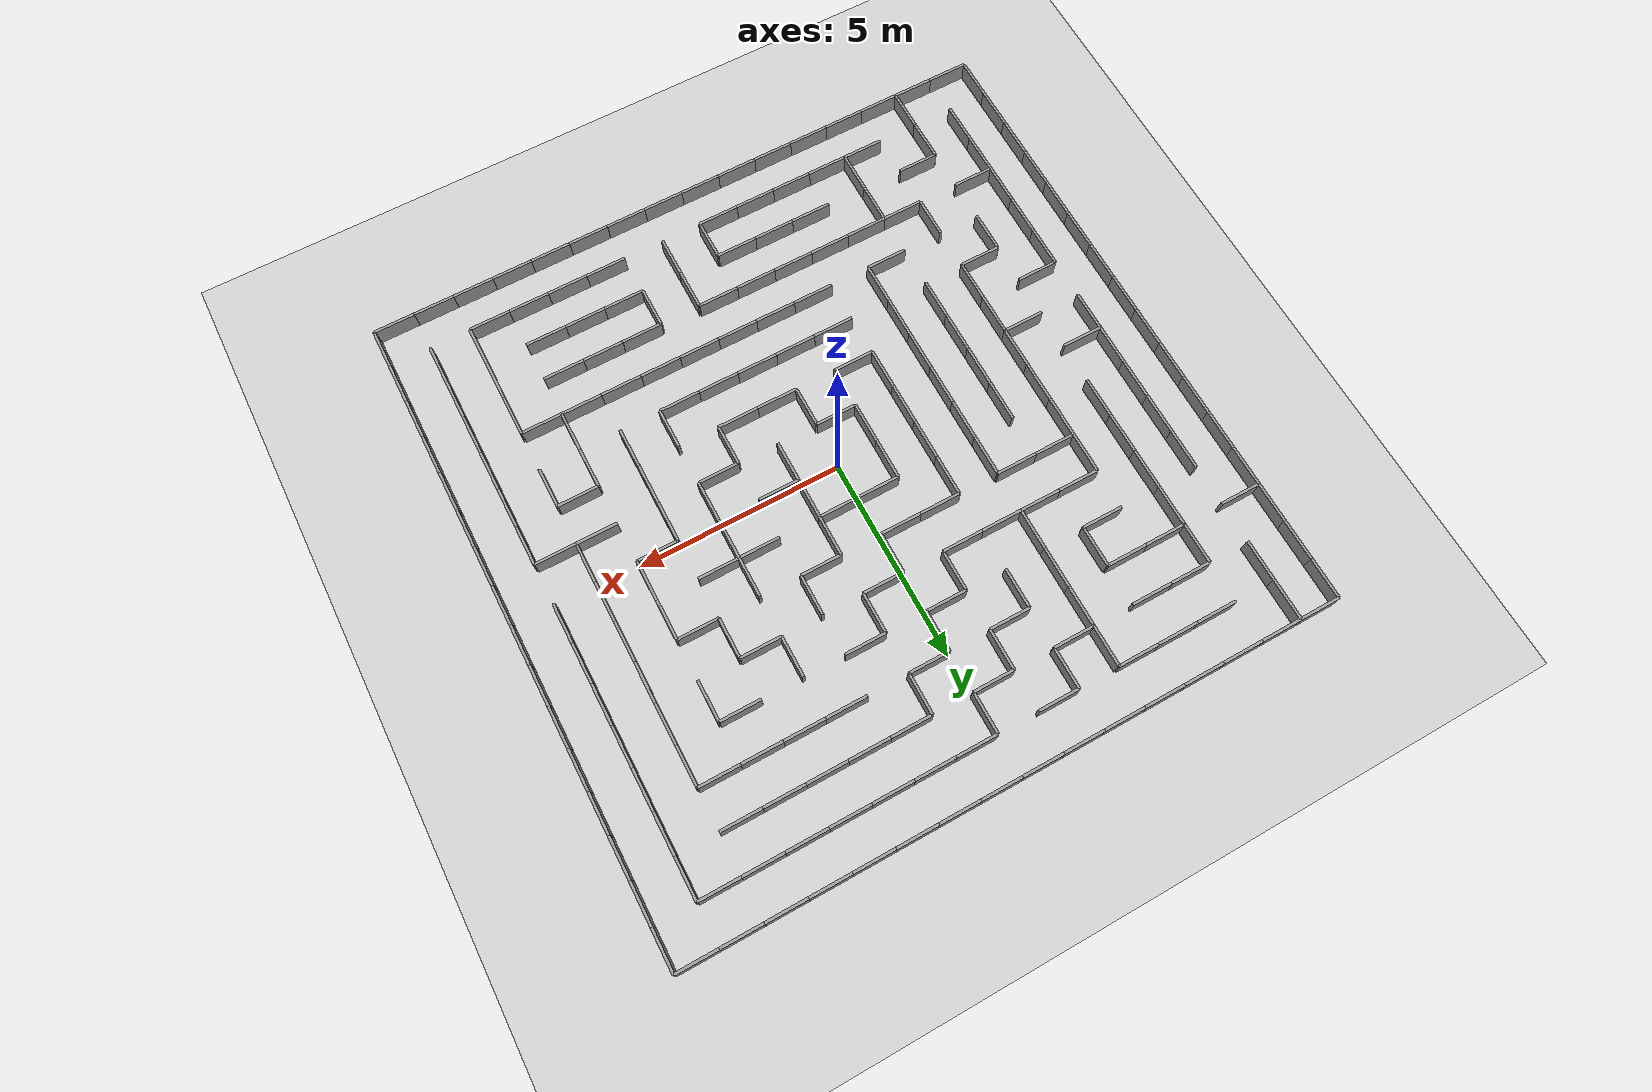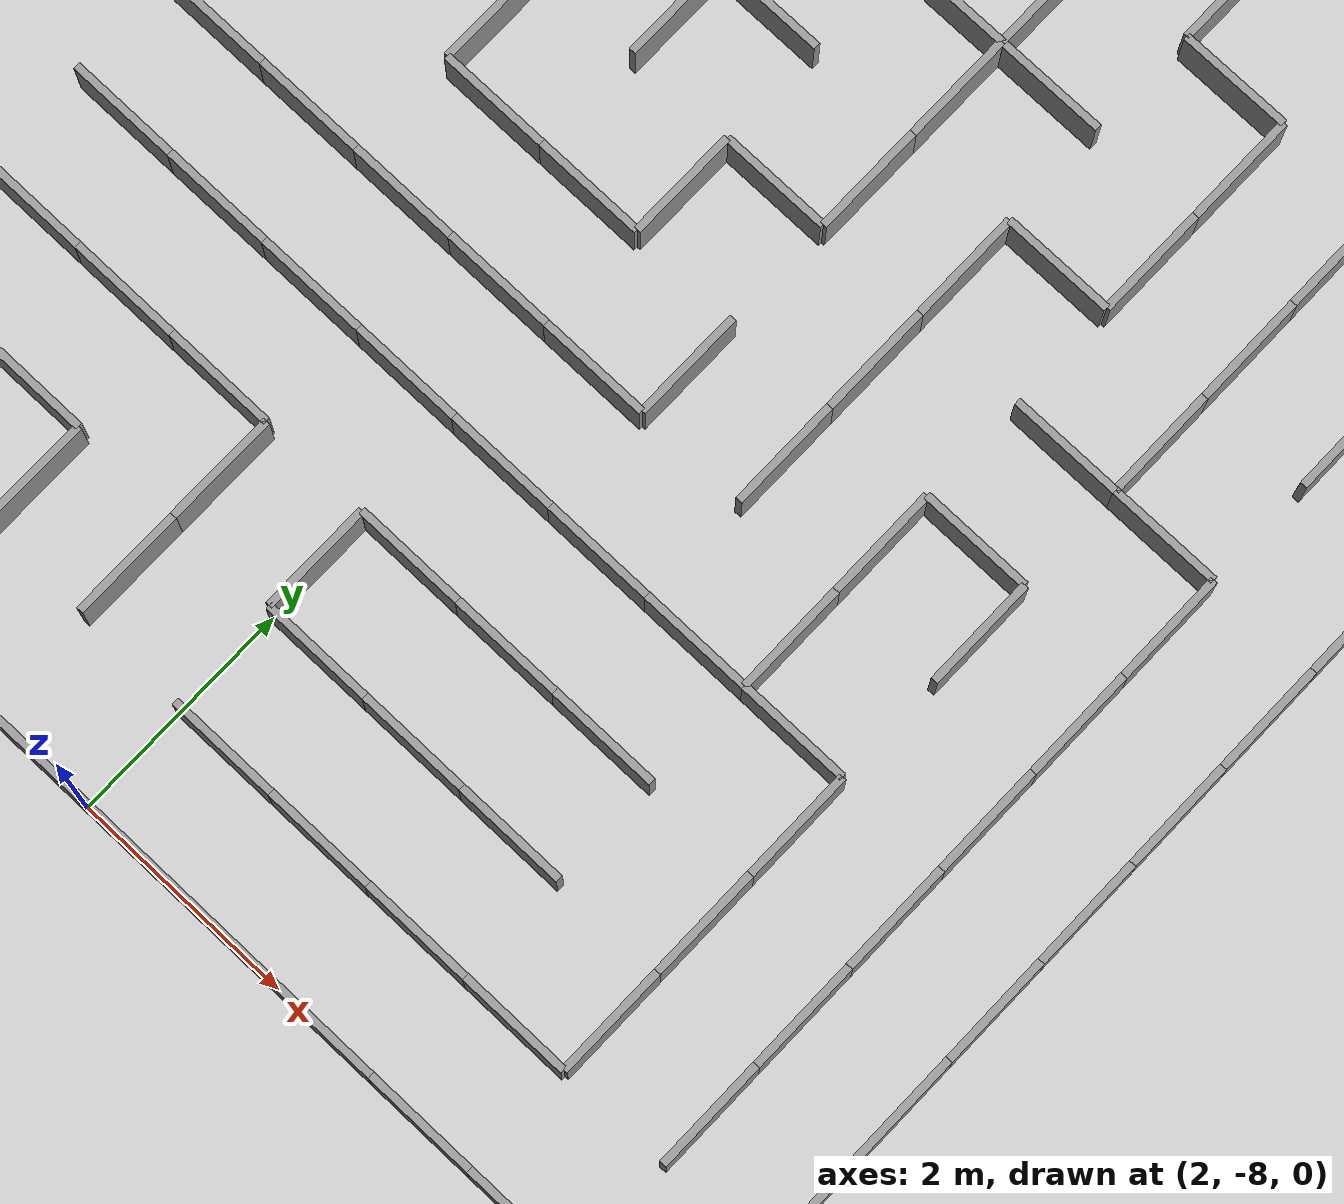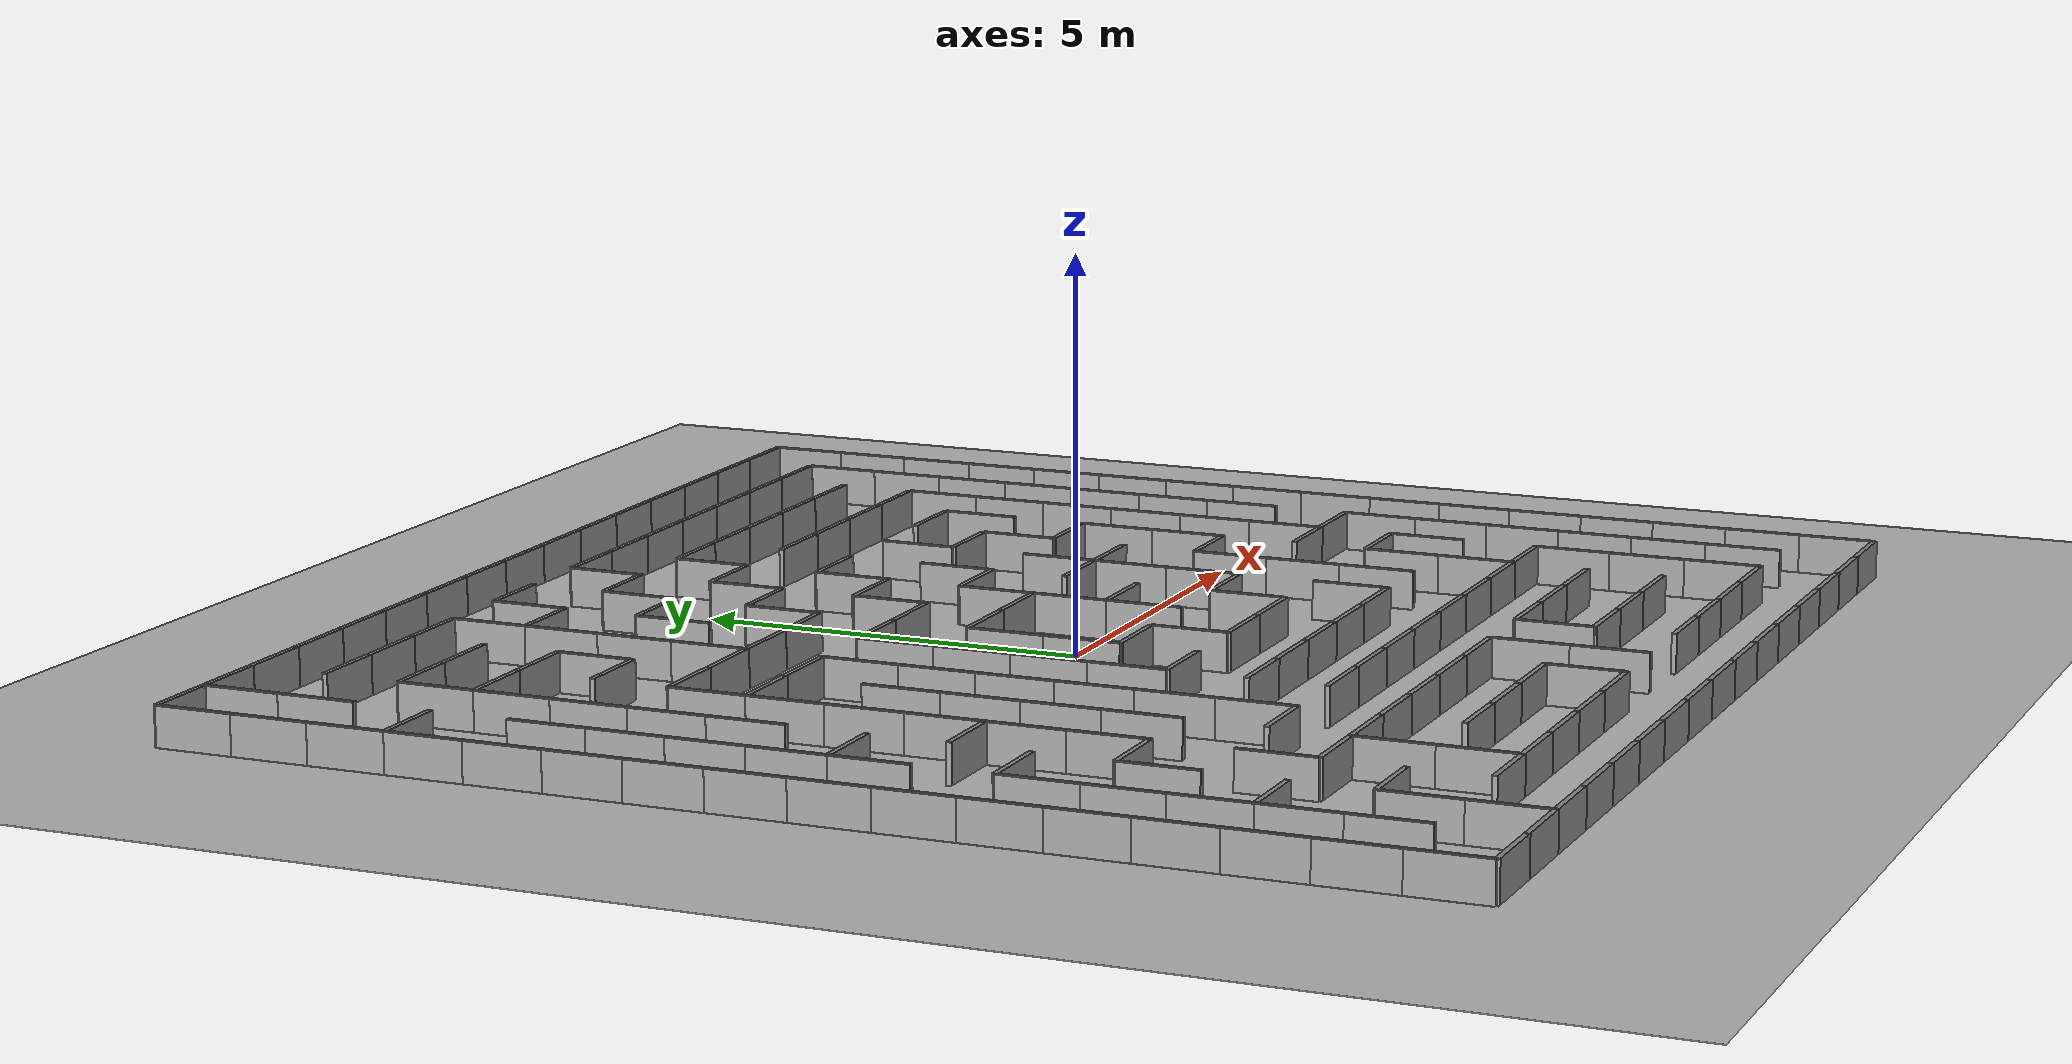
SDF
<?xml version="1.0" ?>
<sdf version="1.7">
  <world name="maze_world">

    <plugin name="gazebo_ros_state" filename="libgazebo_ros_state.so">
      <ros>
        <namespace>/gazebo</namespace>
      </ros>
    </plugin>

    <include>
      <uri>model://sun</uri>
    </include>

    <include>
      <uri>model://ground_plane</uri>
    </include>

    <physics name="default_physics" default="0" type="ode">
      <ode>
        <solver>
          <type>quick</type>
          <iters>10</iters>
          <rms_error>0.0</rms_error>
        </solver>
        <constraints>
          <cfm>0.0</cfm>
          <erp>0.2</erp>
        </constraints>
      </ode>
      <real_time_update_rate>0.0</real_time_update_rate>
      <max_step_size>0.001</max_step_size>
    </physics>

    <gravity>0 0 -9.8</gravity>

    <scene>
      <ambient>0.4 0.4 0.4 1</ambient>
      <background>0.7 0.7 0.7 1</background>
      <shadows>true</shadows>
    </scene>

      <model name="wall_0">
        <static>true</static> <pose>-7.5 8.0 0.25 0 0 0</pose>
        <link name="link">
          <collision name="collision">
            <geometry>
              <box>
                <size>1.0 0.066 0.5</size>
              </box>
            </geometry>
          </collision>
          <visual name="visual">
            <geometry>
              <box>
                <size>1.0 0.066 0.5</size>
              </box>
            </geometry>
            <material>
               <script>
                 <uri>file://media/materials/scripts/gazebo.material</uri>
                 <name>Gazebo/Grey</name> </script>
            </material>
          </visual>
        </link>
      </model>

      <model name="wall_1">
        <static>true</static> <pose>-6.5 8.0 0.25 0 0 0</pose>
        <link name="link">
          <collision name="collision">
            <geometry>
              <box>
                <size>1.0 0.066 0.5</size>
              </box>
            </geometry>
          </collision>
          <visual name="visual">
            <geometry>
              <box>
                <size>1.0 0.066 0.5</size>
              </box>
            </geometry>
            <material>
               <script>
                 <uri>file://media/materials/scripts/gazebo.material</uri>
                 <name>Gazebo/Grey</name> </script>
            </material>
          </visual>
        </link>
      </model>

      <model name="wall_2">
        <static>true</static> <pose>-5.5 8.0 0.25 0 0 0</pose>
        <link name="link">
          <collision name="collision">
            <geometry>
              <box>
                <size>1.0 0.066 0.5</size>
              </box>
            </geometry>
          </collision>
          <visual name="visual">
            <geometry>
              <box>
                <size>1.0 0.066 0.5</size>
              </box>
            </geometry>
            <material>
               <script>
                 <uri>file://media/materials/scripts/gazebo.material</uri>
                 <name>Gazebo/Grey</name> </script>
            </material>
          </visual>
        </link>
      </model>

      <model name="wall_3">
        <static>true</static> <pose>-4.5 8.0 0.25 0 0 0</pose>
        <link name="link">
          <collision name="collision">
            <geometry>
              <box>
                <size>1.0 0.066 0.5</size>
              </box>
            </geometry>
          </collision>
          <visual name="visual">
            <geometry>
              <box>
                <size>1.0 0.066 0.5</size>
              </box>
            </geometry>
            <material>
               <script>
                 <uri>file://media/materials/scripts/gazebo.material</uri>
                 <name>Gazebo/Grey</name> </script>
            </material>
          </visual>
        </link>
      </model>

      <model name="wall_4">
        <static>true</static> <pose>-3.5 8.0 0.25 0 0 0</pose>
        <link name="link">
          <collision name="collision">
            <geometry>
              <box>
                <size>1.0 0.066 0.5</size>
              </box>
            </geometry>
          </collision>
          <visual name="visual">
            <geometry>
              <box>
                <size>1.0 0.066 0.5</size>
              </box>
            </geometry>
            <material>
               <script>
                 <uri>file://media/materials/scripts/gazebo.material</uri>
                 <name>Gazebo/Grey</name> </script>
            </material>
          </visual>
        </link>
      </model>

      <model name="wall_5">
        <static>true</static> <pose>-2.5 8.0 0.25 0 0 0</pose>
        <link name="link">
          <collision name="collision">
            <geometry>
              <box>
                <size>1.0 0.066 0.5</size>
              </box>
            </geometry>
          </collision>
          <visual name="visual">
            <geometry>
              <box>
                <size>1.0 0.066 0.5</size>
              </box>
            </geometry>
            <material>
               <script>
                 <uri>file://media/materials/scripts/gazebo.material</uri>
                 <name>Gazebo/Grey</name> </script>
            </material>
          </visual>
        </link>
      </model>

      <model name="wall_6">
        <static>true</static> <pose>-1.5 8.0 0.25 0 0 0</pose>
        <link name="link">
          <collision name="collision">
            <geometry>
              <box>
                <size>1.0 0.066 0.5</size>
              </box>
            </geometry>
          </collision>
          <visual name="visual">
            <geometry>
              <box>
                <size>1.0 0.066 0.5</size>
              </box>
            </geometry>
            <material>
               <script>
                 <uri>file://media/materials/scripts/gazebo.material</uri>
                 <name>Gazebo/Grey</name> </script>
            </material>
          </visual>
        </link>
      </model>

      <model name="wall_7">
        <static>true</static> <pose>-0.5 8.0 0.25 0 0 0</pose>
        <link name="link">
          <collision name="collision">
            <geometry>
              <box>
                <size>1.0 0.066 0.5</size>
              </box>
            </geometry>
          </collision>
          <visual name="visual">
            <geometry>
              <box>
                <size>1.0 0.066 0.5</size>
              </box>
            </geometry>
            <material>
               <script>
                 <uri>file://media/materials/scripts/gazebo.material</uri>
                 <name>Gazebo/Grey</name> </script>
            </material>
          </visual>
        </link>
      </model>

      <model name="wall_8">
        <static>true</static> <pose>0.5 8.0 0.25 0 0 0</pose>
        <link name="link">
          <collision name="collision">
            <geometry>
              <box>
                <size>1.0 0.066 0.5</size>
              </box>
            </geometry>
          </collision>
          <visual name="visual">
            <geometry>
              <box>
                <size>1.0 0.066 0.5</size>
              </box>
            </geometry>
            <material>
               <script>
                 <uri>file://media/materials/scripts/gazebo.material</uri>
                 <name>Gazebo/Grey</name> </script>
            </material>
          </visual>
        </link>
      </model>

      <model name="wall_9">
        <static>true</static> <pose>1.5 8.0 0.25 0 0 0</pose>
        <link name="link">
          <collision name="collision">
            <geometry>
              <box>
                <size>1.0 0.066 0.5</size>
              </box>
            </geometry>
          </collision>
          <visual name="visual">
            <geometry>
              <box>
                <size>1.0 0.066 0.5</size>
              </box>
            </geometry>
            <material>
               <script>
                 <uri>file://media/materials/scripts/gazebo.material</uri>
                 <name>Gazebo/Grey</name> </script>
            </material>
          </visual>
        </link>
      </model>

      <model name="wall_10">
        <static>true</static> <pose>2.5 8.0 0.25 0 0 0</pose>
        <link name="link">
          <collision name="collision">
            <geometry>
              <box>
                <size>1.0 0.066 0.5</size>
              </box>
            </geometry>
          </collision>
          <visual name="visual">
            <geometry>
              <box>
                <size>1.0 0.066 0.5</size>
              </box>
            </geometry>
            <material>
               <script>
                 <uri>file://media/materials/scripts/gazebo.material</uri>
                 <name>Gazebo/Grey</name> </script>
            </material>
          </visual>
        </link>
      </model>

      <model name="wall_11">
        <static>true</static> <pose>3.5 8.0 0.25 0 0 0</pose>
        <link name="link">
          <collision name="collision">
            <geometry>
              <box>
                <size>1.0 0.066 0.5</size>
              </box>
            </geometry>
          </collision>
          <visual name="visual">
            <geometry>
              <box>
                <size>1.0 0.066 0.5</size>
              </box>
            </geometry>
            <material>
               <script>
                 <uri>file://media/materials/scripts/gazebo.material</uri>
                 <name>Gazebo/Grey</name> </script>
            </material>
          </visual>
        </link>
      </model>

      <model name="wall_12">
        <static>true</static> <pose>4.5 8.0 0.25 0 0 0</pose>
        <link name="link">
          <collision name="collision">
            <geometry>
              <box>
                <size>1.0 0.066 0.5</size>
              </box>
            </geometry>
          </collision>
          <visual name="visual">
            <geometry>
              <box>
                <size>1.0 0.066 0.5</size>
              </box>
            </geometry>
            <material>
               <script>
                 <uri>file://media/materials/scripts/gazebo.material</uri>
                 <name>Gazebo/Grey</name> </script>
            </material>
          </visual>
        </link>
      </model>

      <model name="wall_13">
        <static>true</static> <pose>5.5 8.0 0.25 0 0 0</pose>
        <link name="link">
          <collision name="collision">
            <geometry>
              <box>
                <size>1.0 0.066 0.5</size>
              </box>
            </geometry>
          </collision>
          <visual name="visual">
            <geometry>
              <box>
                <size>1.0 0.066 0.5</size>
              </box>
            </geometry>
            <material>
               <script>
                 <uri>file://media/materials/scripts/gazebo.material</uri>
                 <name>Gazebo/Grey</name> </script>
            </material>
          </visual>
        </link>
      </model>

      <model name="wall_14">
        <static>true</static> <pose>6.5 8.0 0.25 0 0 0</pose>
        <link name="link">
          <collision name="collision">
            <geometry>
              <box>
                <size>1.0 0.066 0.5</size>
              </box>
            </geometry>
          </collision>
          <visual name="visual">
            <geometry>
              <box>
                <size>1.0 0.066 0.5</size>
              </box>
            </geometry>
            <material>
               <script>
                 <uri>file://media/materials/scripts/gazebo.material</uri>
                 <name>Gazebo/Grey</name> </script>
            </material>
          </visual>
        </link>
      </model>

      <model name="wall_15">
        <static>true</static> <pose>7.5 8.0 0.25 0 0 0</pose>
        <link name="link">
          <collision name="collision">
            <geometry>
              <box>
                <size>1.0 0.066 0.5</size>
              </box>
            </geometry>
          </collision>
          <visual name="visual">
            <geometry>
              <box>
                <size>1.0 0.066 0.5</size>
              </box>
            </geometry>
            <material>
               <script>
                 <uri>file://media/materials/scripts/gazebo.material</uri>
                 <name>Gazebo/Grey</name> </script>
            </material>
          </visual>
        </link>
      </model>

      <model name="wall_16">
        <static>true</static> <pose>-8.0 7.5 0.25 0 0 1.5707963267948966</pose>
        <link name="link">
          <collision name="collision">
            <geometry>
              <box>
                <size>1.0 0.066 0.5</size>
              </box>
            </geometry>
          </collision>
          <visual name="visual">
            <geometry>
              <box>
                <size>1.0 0.066 0.5</size>
              </box>
            </geometry>
            <material>
               <script>
                 <uri>file://media/materials/scripts/gazebo.material</uri>
                 <name>Gazebo/Grey</name> </script>
            </material>
          </visual>
        </link>
      </model>

      <model name="wall_17">
        <static>true</static> <pose>-7.0 7.5 0.25 0 0 1.5707963267948966</pose>
        <link name="link">
          <collision name="collision">
            <geometry>
              <box>
                <size>1.0 0.066 0.5</size>
              </box>
            </geometry>
          </collision>
          <visual name="visual">
            <geometry>
              <box>
                <size>1.0 0.066 0.5</size>
              </box>
            </geometry>
            <material>
               <script>
                 <uri>file://media/materials/scripts/gazebo.material</uri>
                 <name>Gazebo/Grey</name> </script>
            </material>
          </visual>
        </link>
      </model>

      <model name="wall_18">
        <static>true</static> <pose>8.0 7.5 0.25 0 0 1.5707963267948966</pose>
        <link name="link">
          <collision name="collision">
            <geometry>
              <box>
                <size>1.0 0.066 0.5</size>
              </box>
            </geometry>
          </collision>
          <visual name="visual">
            <geometry>
              <box>
                <size>1.0 0.066 0.5</size>
              </box>
            </geometry>
            <material>
               <script>
                 <uri>file://media/materials/scripts/gazebo.material</uri>
                 <name>Gazebo/Grey</name> </script>
            </material>
          </visual>
        </link>
      </model>

      <model name="wall_19">
        <static>true</static> <pose>-5.5 7.0 0.25 0 0 0</pose>
        <link name="link">
          <collision name="collision">
            <geometry>
              <box>
                <size>1.0 0.066 0.5</size>
              </box>
            </geometry>
          </collision>
          <visual name="visual">
            <geometry>
              <box>
                <size>1.0 0.066 0.5</size>
              </box>
            </geometry>
            <material>
               <script>
                 <uri>file://media/materials/scripts/gazebo.material</uri>
                 <name>Gazebo/Grey</name> </script>
            </material>
          </visual>
        </link>
      </model>

      <model name="wall_20">
        <static>true</static> <pose>-4.5 7.0 0.25 0 0 0</pose>
        <link name="link">
          <collision name="collision">
            <geometry>
              <box>
                <size>1.0 0.066 0.5</size>
              </box>
            </geometry>
          </collision>
          <visual name="visual">
            <geometry>
              <box>
                <size>1.0 0.066 0.5</size>
              </box>
            </geometry>
            <material>
               <script>
                 <uri>file://media/materials/scripts/gazebo.material</uri>
                 <name>Gazebo/Grey</name> </script>
            </material>
          </visual>
        </link>
      </model>

      <model name="wall_21">
        <static>true</static> <pose>-3.5 7.0 0.25 0 0 0</pose>
        <link name="link">
          <collision name="collision">
            <geometry>
              <box>
                <size>1.0 0.066 0.5</size>
              </box>
            </geometry>
          </collision>
          <visual name="visual">
            <geometry>
              <box>
                <size>1.0 0.066 0.5</size>
              </box>
            </geometry>
            <material>
               <script>
                 <uri>file://media/materials/scripts/gazebo.material</uri>
                 <name>Gazebo/Grey</name> </script>
            </material>
          </visual>
        </link>
      </model>

      <model name="wall_22">
        <static>true</static> <pose>-1.5 7.0 0.25 0 0 0</pose>
        <link name="link">
          <collision name="collision">
            <geometry>
              <box>
                <size>1.0 0.066 0.5</size>
              </box>
            </geometry>
          </collision>
          <visual name="visual">
            <geometry>
              <box>
                <size>1.0 0.066 0.5</size>
              </box>
            </geometry>
            <material>
               <script>
                 <uri>file://media/materials/scripts/gazebo.material</uri>
                 <name>Gazebo/Grey</name> </script>
            </material>
          </visual>
        </link>
      </model>

      <model name="wall_23">
        <static>true</static> <pose>0.5 7.0 0.25 0 0 0</pose>
        <link name="link">
          <collision name="collision">
            <geometry>
              <box>
                <size>1.0 0.066 0.5</size>
              </box>
            </geometry>
          </collision>
          <visual name="visual">
            <geometry>
              <box>
                <size>1.0 0.066 0.5</size>
              </box>
            </geometry>
            <material>
               <script>
                 <uri>file://media/materials/scripts/gazebo.material</uri>
                 <name>Gazebo/Grey</name> </script>
            </material>
          </visual>
        </link>
      </model>

      <model name="wall_24">
        <static>true</static> <pose>1.5 7.0 0.25 0 0 0</pose>
        <link name="link">
          <collision name="collision">
            <geometry>
              <box>
                <size>1.0 0.066 0.5</size>
              </box>
            </geometry>
          </collision>
          <visual name="visual">
            <geometry>
              <box>
                <size>1.0 0.066 0.5</size>
              </box>
            </geometry>
            <material>
               <script>
                 <uri>file://media/materials/scripts/gazebo.material</uri>
                 <name>Gazebo/Grey</name> </script>
            </material>
          </visual>
        </link>
      </model>

      <model name="wall_25">
        <static>true</static> <pose>2.5 7.0 0.25 0 0 0</pose>
        <link name="link">
          <collision name="collision">
            <geometry>
              <box>
                <size>1.0 0.066 0.5</size>
              </box>
            </geometry>
          </collision>
          <visual name="visual">
            <geometry>
              <box>
                <size>1.0 0.066 0.5</size>
              </box>
            </geometry>
            <material>
               <script>
                 <uri>file://media/materials/scripts/gazebo.material</uri>
                 <name>Gazebo/Grey</name> </script>
            </material>
          </visual>
        </link>
      </model>

      <model name="wall_26">
        <static>true</static> <pose>3.5 7.0 0.25 0 0 0</pose>
        <link name="link">
          <collision name="collision">
            <geometry>
              <box>
                <size>1.0 0.066 0.5</size>
              </box>
            </geometry>
          </collision>
          <visual name="visual">
            <geometry>
              <box>
                <size>1.0 0.066 0.5</size>
              </box>
            </geometry>
            <material>
               <script>
                 <uri>file://media/materials/scripts/gazebo.material</uri>
                 <name>Gazebo/Grey</name> </script>
            </material>
          </visual>
        </link>
      </model>

      <model name="wall_27">
        <static>true</static> <pose>4.5 7.0 0.25 0 0 0</pose>
        <link name="link">
          <collision name="collision">
            <geometry>
              <box>
                <size>1.0 0.066 0.5</size>
              </box>
            </geometry>
          </collision>
          <visual name="visual">
            <geometry>
              <box>
                <size>1.0 0.066 0.5</size>
              </box>
            </geometry>
            <material>
               <script>
                 <uri>file://media/materials/scripts/gazebo.material</uri>
                 <name>Gazebo/Grey</name> </script>
            </material>
          </visual>
        </link>
      </model>

      <model name="wall_28">
        <static>true</static> <pose>5.5 7.0 0.25 0 0 0</pose>
        <link name="link">
          <collision name="collision">
            <geometry>
              <box>
                <size>1.0 0.066 0.5</size>
              </box>
            </geometry>
          </collision>
          <visual name="visual">
            <geometry>
              <box>
                <size>1.0 0.066 0.5</size>
              </box>
            </geometry>
            <material>
               <script>
                 <uri>file://media/materials/scripts/gazebo.material</uri>
                 <name>Gazebo/Grey</name> </script>
            </material>
          </visual>
        </link>
      </model>

      <model name="wall_29">
        <static>true</static> <pose>6.5 7.0 0.25 0 0 0</pose>
        <link name="link">
          <collision name="collision">
            <geometry>
              <box>
                <size>1.0 0.066 0.5</size>
              </box>
            </geometry>
          </collision>
          <visual name="visual">
            <geometry>
              <box>
                <size>1.0 0.066 0.5</size>
              </box>
            </geometry>
            <material>
               <script>
                 <uri>file://media/materials/scripts/gazebo.material</uri>
                 <name>Gazebo/Grey</name> </script>
            </material>
          </visual>
        </link>
      </model>

      <model name="wall_30">
        <static>true</static> <pose>-8.0 6.5 0.25 0 0 1.5707963267948966</pose>
        <link name="link">
          <collision name="collision">
            <geometry>
              <box>
                <size>1.0 0.066 0.5</size>
              </box>
            </geometry>
          </collision>
          <visual name="visual">
            <geometry>
              <box>
                <size>1.0 0.066 0.5</size>
              </box>
            </geometry>
            <material>
               <script>
                 <uri>file://media/materials/scripts/gazebo.material</uri>
                 <name>Gazebo/Grey</name> </script>
            </material>
          </visual>
        </link>
      </model>

      <model name="wall_31">
        <static>true</static> <pose>-7.0 6.5 0.25 0 0 1.5707963267948966</pose>
        <link name="link">
          <collision name="collision">
            <geometry>
              <box>
                <size>1.0 0.066 0.5</size>
              </box>
            </geometry>
          </collision>
          <visual name="visual">
            <geometry>
              <box>
                <size>1.0 0.066 0.5</size>
              </box>
            </geometry>
            <material>
               <script>
                 <uri>file://media/materials/scripts/gazebo.material</uri>
                 <name>Gazebo/Grey</name> </script>
            </material>
          </visual>
        </link>
      </model>

      <model name="wall_32">
        <static>true</static> <pose>-3.0 6.5 0.25 0 0 1.5707963267948966</pose>
        <link name="link">
          <collision name="collision">
            <geometry>
              <box>
                <size>1.0 0.066 0.5</size>
              </box>
            </geometry>
          </collision>
          <visual name="visual">
            <geometry>
              <box>
                <size>1.0 0.066 0.5</size>
              </box>
            </geometry>
            <material>
               <script>
                 <uri>file://media/materials/scripts/gazebo.material</uri>
                 <name>Gazebo/Grey</name> </script>
            </material>
          </visual>
        </link>
      </model>

      <model name="wall_33">
        <static>true</static> <pose>-2.0 6.5 0.25 0 0 1.5707963267948966</pose>
        <link name="link">
          <collision name="collision">
            <geometry>
              <box>
                <size>1.0 0.066 0.5</size>
              </box>
            </geometry>
          </collision>
          <visual name="visual">
            <geometry>
              <box>
                <size>1.0 0.066 0.5</size>
              </box>
            </geometry>
            <material>
               <script>
                 <uri>file://media/materials/scripts/gazebo.material</uri>
                 <name>Gazebo/Grey</name> </script>
            </material>
          </visual>
        </link>
      </model>

      <model name="wall_34">
        <static>true</static> <pose>0.0 6.5 0.25 0 0 1.5707963267948966</pose>
        <link name="link">
          <collision name="collision">
            <geometry>
              <box>
                <size>1.0 0.066 0.5</size>
              </box>
            </geometry>
          </collision>
          <visual name="visual">
            <geometry>
              <box>
                <size>1.0 0.066 0.5</size>
              </box>
            </geometry>
            <material>
               <script>
                 <uri>file://media/materials/scripts/gazebo.material</uri>
                 <name>Gazebo/Grey</name> </script>
            </material>
          </visual>
        </link>
      </model>

      <model name="wall_35">
        <static>true</static> <pose>7.0 6.5 0.25 0 0 1.5707963267948966</pose>
        <link name="link">
          <collision name="collision">
            <geometry>
              <box>
                <size>1.0 0.066 0.5</size>
              </box>
            </geometry>
          </collision>
          <visual name="visual">
            <geometry>
              <box>
                <size>1.0 0.066 0.5</size>
              </box>
            </geometry>
            <material>
               <script>
                 <uri>file://media/materials/scripts/gazebo.material</uri>
                 <name>Gazebo/Grey</name> </script>
            </material>
          </visual>
        </link>
      </model>

      <model name="wall_36">
        <static>true</static> <pose>8.0 6.5 0.25 0 0 1.5707963267948966</pose>
        <link name="link">
          <collision name="collision">
            <geometry>
              <box>
                <size>1.0 0.066 0.5</size>
              </box>
            </geometry>
          </collision>
          <visual name="visual">
            <geometry>
              <box>
                <size>1.0 0.066 0.5</size>
              </box>
            </geometry>
            <material>
               <script>
                 <uri>file://media/materials/scripts/gazebo.material</uri>
                 <name>Gazebo/Grey</name> </script>
            </material>
          </visual>
        </link>
      </model>

      <model name="wall_37">
        <static>true</static> <pose>-5.5 6.0 0.25 0 0 0</pose>
        <link name="link">
          <collision name="collision">
            <geometry>
              <box>
                <size>1.0 0.066 0.5</size>
              </box>
            </geometry>
          </collision>
          <visual name="visual">
            <geometry>
              <box>
                <size>1.0 0.066 0.5</size>
              </box>
            </geometry>
            <material>
               <script>
                 <uri>file://media/materials/scripts/gazebo.material</uri>
                 <name>Gazebo/Grey</name> </script>
            </material>
          </visual>
        </link>
      </model>

      <model name="wall_38">
        <static>true</static> <pose>-4.5 6.0 0.25 0 0 0</pose>
        <link name="link">
          <collision name="collision">
            <geometry>
              <box>
                <size>1.0 0.066 0.5</size>
              </box>
            </geometry>
          </collision>
          <visual name="visual">
            <geometry>
              <box>
                <size>1.0 0.066 0.5</size>
              </box>
            </geometry>
            <material>
               <script>
                 <uri>file://media/materials/scripts/gazebo.material</uri>
                 <name>Gazebo/Grey</name> </script>
            </material>
          </visual>
        </link>
      </model>

      <model name="wall_39">
        <static>true</static> <pose>-2.5 6.0 0.25 0 0 0</pose>
        <link name="link">
          <collision name="collision">
            <geometry>
              <box>
                <size>1.0 0.066 0.5</size>
              </box>
            </geometry>
          </collision>
          <visual name="visual">
            <geometry>
              <box>
                <size>1.0 0.066 0.5</size>
              </box>
            </geometry>
            <material>
               <script>
                 <uri>file://media/materials/scripts/gazebo.material</uri>
                 <name>Gazebo/Grey</name> </script>
            </material>
          </visual>
        </link>
      </model>

      <model name="wall_40">
        <static>true</static> <pose>-0.5 6.0 0.25 0 0 0</pose>
        <link name="link">
          <collision name="collision">
            <geometry>
              <box>
                <size>1.0 0.066 0.5</size>
              </box>
            </geometry>
          </collision>
          <visual name="visual">
            <geometry>
              <box>
                <size>1.0 0.066 0.5</size>
              </box>
            </geometry>
            <material>
               <script>
                 <uri>file://media/materials/scripts/gazebo.material</uri>
                 <name>Gazebo/Grey</name> </script>
            </material>
          </visual>
        </link>
      </model>

      <model name="wall_41">
        <static>true</static> <pose>1.5 6.0 0.25 0 0 0</pose>
        <link name="link">
          <collision name="collision">
            <geometry>
              <box>
                <size>1.0 0.066 0.5</size>
              </box>
            </geometry>
          </collision>
          <visual name="visual">
            <geometry>
              <box>
                <size>1.0 0.066 0.5</size>
              </box>
            </geometry>
            <material>
               <script>
                 <uri>file://media/materials/scripts/gazebo.material</uri>
                 <name>Gazebo/Grey</name> </script>
            </material>
          </visual>
        </link>
      </model>

      <model name="wall_42">
        <static>true</static> <pose>2.5 6.0 0.25 0 0 0</pose>
        <link name="link">
          <collision name="collision">
            <geometry>
              <box>
                <size>1.0 0.066 0.5</size>
              </box>
            </geometry>
          </collision>
          <visual name="visual">
            <geometry>
              <box>
                <size>1.0 0.066 0.5</size>
              </box>
            </geometry>
            <material>
               <script>
                 <uri>file://media/materials/scripts/gazebo.material</uri>
                 <name>Gazebo/Grey</name> </script>
            </material>
          </visual>
        </link>
      </model>

      <model name="wall_43">
        <static>true</static> <pose>3.5 6.0 0.25 0 0 0</pose>
        <link name="link">
          <collision name="collision">
            <geometry>
              <box>
                <size>1.0 0.066 0.5</size>
              </box>
            </geometry>
          </collision>
          <visual name="visual">
            <geometry>
              <box>
                <size>1.0 0.066 0.5</size>
              </box>
            </geometry>
            <material>
               <script>
                 <uri>file://media/materials/scripts/gazebo.material</uri>
                 <name>Gazebo/Grey</name> </script>
            </material>
          </visual>
        </link>
      </model>

      <model name="wall_44">
        <static>true</static> <pose>4.5 6.0 0.25 0 0 0</pose>
        <link name="link">
          <collision name="collision">
            <geometry>
              <box>
                <size>1.0 0.066 0.5</size>
              </box>
            </geometry>
          </collision>
          <visual name="visual">
            <geometry>
              <box>
                <size>1.0 0.066 0.5</size>
              </box>
            </geometry>
            <material>
               <script>
                 <uri>file://media/materials/scripts/gazebo.material</uri>
                 <name>Gazebo/Grey</name> </script>
            </material>
          </visual>
        </link>
      </model>

      <model name="wall_45">
        <static>true</static> <pose>5.5 6.0 0.25 0 0 0</pose>
        <link name="link">
          <collision name="collision">
            <geometry>
              <box>
                <size>1.0 0.066 0.5</size>
              </box>
            </geometry>
          </collision>
          <visual name="visual">
            <geometry>
              <box>
                <size>1.0 0.066 0.5</size>
              </box>
            </geometry>
            <material>
               <script>
                 <uri>file://media/materials/scripts/gazebo.material</uri>
                 <name>Gazebo/Grey</name> </script>
            </material>
          </visual>
        </link>
      </model>

      <model name="wall_46">
        <static>true</static> <pose>-8.0 5.5 0.25 0 0 1.5707963267948966</pose>
        <link name="link">
          <collision name="collision">
            <geometry>
              <box>
                <size>1.0 0.066 0.5</size>
              </box>
            </geometry>
          </collision>
          <visual name="visual">
            <geometry>
              <box>
                <size>1.0 0.066 0.5</size>
              </box>
            </geometry>
            <material>
               <script>
                 <uri>file://media/materials/scripts/gazebo.material</uri>
                 <name>Gazebo/Grey</name> </script>
            </material>
          </visual>
        </link>
      </model>

      <model name="wall_47">
        <static>true</static> <pose>-6.0 5.5 0.25 0 0 1.5707963267948966</pose>
        <link name="link">
          <collision name="collision">
            <geometry>
              <box>
                <size>1.0 0.066 0.5</size>
              </box>
            </geometry>
          </collision>
          <visual name="visual">
            <geometry>
              <box>
                <size>1.0 0.066 0.5</size>
              </box>
            </geometry>
            <material>
               <script>
                 <uri>file://media/materials/scripts/gazebo.material</uri>
                 <name>Gazebo/Grey</name> </script>
            </material>
          </visual>
        </link>
      </model>

      <model name="wall_48">
        <static>true</static> <pose>-3.0 5.5 0.25 0 0 1.5707963267948966</pose>
        <link name="link">
          <collision name="collision">
            <geometry>
              <box>
                <size>1.0 0.066 0.5</size>
              </box>
            </geometry>
          </collision>
          <visual name="visual">
            <geometry>
              <box>
                <size>1.0 0.066 0.5</size>
              </box>
            </geometry>
            <material>
               <script>
                 <uri>file://media/materials/scripts/gazebo.material</uri>
                 <name>Gazebo/Grey</name> </script>
            </material>
          </visual>
        </link>
      </model>

      <model name="wall_49">
        <static>true</static> <pose>-1.0 5.5 0.25 0 0 1.5707963267948966</pose>
        <link name="link">
          <collision name="collision">
            <geometry>
              <box>
                <size>1.0 0.066 0.5</size>
              </box>
            </geometry>
          </collision>
          <visual name="visual">
            <geometry>
              <box>
                <size>1.0 0.066 0.5</size>
              </box>
            </geometry>
            <material>
               <script>
                 <uri>file://media/materials/scripts/gazebo.material</uri>
                 <name>Gazebo/Grey</name> </script>
            </material>
          </visual>
        </link>
      </model>

      <model name="wall_50">
        <static>true</static> <pose>1.0 5.5 0.25 0 0 1.5707963267948966</pose>
        <link name="link">
          <collision name="collision">
            <geometry>
              <box>
                <size>1.0 0.066 0.5</size>
              </box>
            </geometry>
          </collision>
          <visual name="visual">
            <geometry>
              <box>
                <size>1.0 0.066 0.5</size>
              </box>
            </geometry>
            <material>
               <script>
                 <uri>file://media/materials/scripts/gazebo.material</uri>
                 <name>Gazebo/Grey</name> </script>
            </material>
          </visual>
        </link>
      </model>

      <model name="wall_51">
        <static>true</static> <pose>7.0 5.5 0.25 0 0 1.5707963267948966</pose>
        <link name="link">
          <collision name="collision">
            <geometry>
              <box>
                <size>1.0 0.066 0.5</size>
              </box>
            </geometry>
          </collision>
          <visual name="visual">
            <geometry>
              <box>
                <size>1.0 0.066 0.5</size>
              </box>
            </geometry>
            <material>
               <script>
                 <uri>file://media/materials/scripts/gazebo.material</uri>
                 <name>Gazebo/Grey</name> </script>
            </material>
          </visual>
        </link>
      </model>

      <model name="wall_52">
        <static>true</static> <pose>8.0 5.5 0.25 0 0 1.5707963267948966</pose>
        <link name="link">
          <collision name="collision">
            <geometry>
              <box>
                <size>1.0 0.066 0.5</size>
              </box>
            </geometry>
          </collision>
          <visual name="visual">
            <geometry>
              <box>
                <size>1.0 0.066 0.5</size>
              </box>
            </geometry>
            <material>
               <script>
                 <uri>file://media/materials/scripts/gazebo.material</uri>
                 <name>Gazebo/Grey</name> </script>
            </material>
          </visual>
        </link>
      </model>

      <model name="wall_53">
        <static>true</static> <pose>-7.5 5.0 0.25 0 0 0</pose>
        <link name="link">
          <collision name="collision">
            <geometry>
              <box>
                <size>1.0 0.066 0.5</size>
              </box>
            </geometry>
          </collision>
          <visual name="visual">
            <geometry>
              <box>
                <size>1.0 0.066 0.5</size>
              </box>
            </geometry>
            <material>
               <script>
                 <uri>file://media/materials/scripts/gazebo.material</uri>
                 <name>Gazebo/Grey</name> </script>
            </material>
          </visual>
        </link>
      </model>

      <model name="wall_54">
        <static>true</static> <pose>-5.5 5.0 0.25 0 0 0</pose>
        <link name="link">
          <collision name="collision">
            <geometry>
              <box>
                <size>1.0 0.066 0.5</size>
              </box>
            </geometry>
          </collision>
          <visual name="visual">
            <geometry>
              <box>
                <size>1.0 0.066 0.5</size>
              </box>
            </geometry>
            <material>
               <script>
                 <uri>file://media/materials/scripts/gazebo.material</uri>
                 <name>Gazebo/Grey</name> </script>
            </material>
          </visual>
        </link>
      </model>

      <model name="wall_55">
        <static>true</static> <pose>-4.5 5.0 0.25 0 0 0</pose>
        <link name="link">
          <collision name="collision">
            <geometry>
              <box>
                <size>1.0 0.066 0.5</size>
              </box>
            </geometry>
          </collision>
          <visual name="visual">
            <geometry>
              <box>
                <size>1.0 0.066 0.5</size>
              </box>
            </geometry>
            <material>
               <script>
                 <uri>file://media/materials/scripts/gazebo.material</uri>
                 <name>Gazebo/Grey</name> </script>
            </material>
          </visual>
        </link>
      </model>

      <model name="wall_56">
        <static>true</static> <pose>-1.5 5.0 0.25 0 0 0</pose>
        <link name="link">
          <collision name="collision">
            <geometry>
              <box>
                <size>1.0 0.066 0.5</size>
              </box>
            </geometry>
          </collision>
          <visual name="visual">
            <geometry>
              <box>
                <size>1.0 0.066 0.5</size>
              </box>
            </geometry>
            <material>
               <script>
                 <uri>file://media/materials/scripts/gazebo.material</uri>
                 <name>Gazebo/Grey</name> </script>
            </material>
          </visual>
        </link>
      </model>

      <model name="wall_57">
        <static>true</static> <pose>0.5 5.0 0.25 0 0 0</pose>
        <link name="link">
          <collision name="collision">
            <geometry>
              <box>
                <size>1.0 0.066 0.5</size>
              </box>
            </geometry>
          </collision>
          <visual name="visual">
            <geometry>
              <box>
                <size>1.0 0.066 0.5</size>
              </box>
            </geometry>
            <material>
               <script>
                 <uri>file://media/materials/scripts/gazebo.material</uri>
                 <name>Gazebo/Grey</name> </script>
            </material>
          </visual>
        </link>
      </model>

      <model name="wall_58">
        <static>true</static> <pose>2.5 5.0 0.25 0 0 0</pose>
        <link name="link">
          <collision name="collision">
            <geometry>
              <box>
                <size>1.0 0.066 0.5</size>
              </box>
            </geometry>
          </collision>
          <visual name="visual">
            <geometry>
              <box>
                <size>1.0 0.066 0.5</size>
              </box>
            </geometry>
            <material>
               <script>
                 <uri>file://media/materials/scripts/gazebo.material</uri>
                 <name>Gazebo/Grey</name> </script>
            </material>
          </visual>
        </link>
      </model>

      <model name="wall_59">
        <static>true</static> <pose>3.5 5.0 0.25 0 0 0</pose>
        <link name="link">
          <collision name="collision">
            <geometry>
              <box>
                <size>1.0 0.066 0.5</size>
              </box>
            </geometry>
          </collision>
          <visual name="visual">
            <geometry>
              <box>
                <size>1.0 0.066 0.5</size>
              </box>
            </geometry>
            <material>
               <script>
                 <uri>file://media/materials/scripts/gazebo.material</uri>
                 <name>Gazebo/Grey</name> </script>
            </material>
          </visual>
        </link>
      </model>

      <model name="wall_60">
        <static>true</static> <pose>4.5 5.0 0.25 0 0 0</pose>
        <link name="link">
          <collision name="collision">
            <geometry>
              <box>
                <size>1.0 0.066 0.5</size>
              </box>
            </geometry>
          </collision>
          <visual name="visual">
            <geometry>
              <box>
                <size>1.0 0.066 0.5</size>
              </box>
            </geometry>
            <material>
               <script>
                 <uri>file://media/materials/scripts/gazebo.material</uri>
                 <name>Gazebo/Grey</name> </script>
            </material>
          </visual>
        </link>
      </model>

      <model name="wall_61">
        <static>true</static> <pose>5.5 5.0 0.25 0 0 0</pose>
        <link name="link">
          <collision name="collision">
            <geometry>
              <box>
                <size>1.0 0.066 0.5</size>
              </box>
            </geometry>
          </collision>
          <visual name="visual">
            <geometry>
              <box>
                <size>1.0 0.066 0.5</size>
              </box>
            </geometry>
            <material>
               <script>
                 <uri>file://media/materials/scripts/gazebo.material</uri>
                 <name>Gazebo/Grey</name> </script>
            </material>
          </visual>
        </link>
      </model>

      <model name="wall_62">
        <static>true</static> <pose>-8.0 4.5 0.25 0 0 1.5707963267948966</pose>
        <link name="link">
          <collision name="collision">
            <geometry>
              <box>
                <size>1.0 0.066 0.5</size>
              </box>
            </geometry>
          </collision>
          <visual name="visual">
            <geometry>
              <box>
                <size>1.0 0.066 0.5</size>
              </box>
            </geometry>
            <material>
               <script>
                 <uri>file://media/materials/scripts/gazebo.material</uri>
                 <name>Gazebo/Grey</name> </script>
            </material>
          </visual>
        </link>
      </model>

      <model name="wall_63">
        <static>true</static> <pose>-6.0 4.5 0.25 0 0 1.5707963267948966</pose>
        <link name="link">
          <collision name="collision">
            <geometry>
              <box>
                <size>1.0 0.066 0.5</size>
              </box>
            </geometry>
          </collision>
          <visual name="visual">
            <geometry>
              <box>
                <size>1.0 0.066 0.5</size>
              </box>
            </geometry>
            <material>
               <script>
                 <uri>file://media/materials/scripts/gazebo.material</uri>
                 <name>Gazebo/Grey</name> </script>
            </material>
          </visual>
        </link>
      </model>

      <model name="wall_64">
        <static>true</static> <pose>-4.0 4.5 0.25 0 0 1.5707963267948966</pose>
        <link name="link">
          <collision name="collision">
            <geometry>
              <box>
                <size>1.0 0.066 0.5</size>
              </box>
            </geometry>
          </collision>
          <visual name="visual">
            <geometry>
              <box>
                <size>1.0 0.066 0.5</size>
              </box>
            </geometry>
            <material>
               <script>
                 <uri>file://media/materials/scripts/gazebo.material</uri>
                 <name>Gazebo/Grey</name> </script>
            </material>
          </visual>
        </link>
      </model>

      <model name="wall_65">
        <static>true</static> <pose>-3.0 4.5 0.25 0 0 1.5707963267948966</pose>
        <link name="link">
          <collision name="collision">
            <geometry>
              <box>
                <size>1.0 0.066 0.5</size>
              </box>
            </geometry>
          </collision>
          <visual name="visual">
            <geometry>
              <box>
                <size>1.0 0.066 0.5</size>
              </box>
            </geometry>
            <material>
               <script>
                 <uri>file://media/materials/scripts/gazebo.material</uri>
                 <name>Gazebo/Grey</name> </script>
            </material>
          </visual>
        </link>
      </model>

      <model name="wall_66">
        <static>true</static> <pose>-2.0 4.5 0.25 0 0 1.5707963267948966</pose>
        <link name="link">
          <collision name="collision">
            <geometry>
              <box>
                <size>1.0 0.066 0.5</size>
              </box>
            </geometry>
          </collision>
          <visual name="visual">
            <geometry>
              <box>
                <size>1.0 0.066 0.5</size>
              </box>
            </geometry>
            <material>
               <script>
                 <uri>file://media/materials/scripts/gazebo.material</uri>
                 <name>Gazebo/Grey</name> </script>
            </material>
          </visual>
        </link>
      </model>

      <model name="wall_67">
        <static>true</static> <pose>0.0 4.5 0.25 0 0 1.5707963267948966</pose>
        <link name="link">
          <collision name="collision">
            <geometry>
              <box>
                <size>1.0 0.066 0.5</size>
              </box>
            </geometry>
          </collision>
          <visual name="visual">
            <geometry>
              <box>
                <size>1.0 0.066 0.5</size>
              </box>
            </geometry>
            <material>
               <script>
                 <uri>file://media/materials/scripts/gazebo.material</uri>
                 <name>Gazebo/Grey</name> </script>
            </material>
          </visual>
        </link>
      </model>

      <model name="wall_68">
        <static>true</static> <pose>6.0 4.5 0.25 0 0 1.5707963267948966</pose>
        <link name="link">
          <collision name="collision">
            <geometry>
              <box>
                <size>1.0 0.066 0.5</size>
              </box>
            </geometry>
          </collision>
          <visual name="visual">
            <geometry>
              <box>
                <size>1.0 0.066 0.5</size>
              </box>
            </geometry>
            <material>
               <script>
                 <uri>file://media/materials/scripts/gazebo.material</uri>
                 <name>Gazebo/Grey</name> </script>
            </material>
          </visual>
        </link>
      </model>

      <model name="wall_69">
        <static>true</static> <pose>7.0 4.5 0.25 0 0 1.5707963267948966</pose>
        <link name="link">
          <collision name="collision">
            <geometry>
              <box>
                <size>1.0 0.066 0.5</size>
              </box>
            </geometry>
          </collision>
          <visual name="visual">
            <geometry>
              <box>
                <size>1.0 0.066 0.5</size>
              </box>
            </geometry>
            <material>
               <script>
                 <uri>file://media/materials/scripts/gazebo.material</uri>
                 <name>Gazebo/Grey</name> </script>
            </material>
          </visual>
        </link>
      </model>

      <model name="wall_70">
        <static>true</static> <pose>8.0 4.5 0.25 0 0 1.5707963267948966</pose>
        <link name="link">
          <collision name="collision">
            <geometry>
              <box>
                <size>1.0 0.066 0.5</size>
              </box>
            </geometry>
          </collision>
          <visual name="visual">
            <geometry>
              <box>
                <size>1.0 0.066 0.5</size>
              </box>
            </geometry>
            <material>
               <script>
                 <uri>file://media/materials/scripts/gazebo.material</uri>
                 <name>Gazebo/Grey</name> </script>
            </material>
          </visual>
        </link>
      </model>

      <model name="wall_71">
        <static>true</static> <pose>-4.5 4.0 0.25 0 0 0</pose>
        <link name="link">
          <collision name="collision">
            <geometry>
              <box>
                <size>1.0 0.066 0.5</size>
              </box>
            </geometry>
          </collision>
          <visual name="visual">
            <geometry>
              <box>
                <size>1.0 0.066 0.5</size>
              </box>
            </geometry>
            <material>
               <script>
                 <uri>file://media/materials/scripts/gazebo.material</uri>
                 <name>Gazebo/Grey</name> </script>
            </material>
          </visual>
        </link>
      </model>

      <model name="wall_72">
        <static>true</static> <pose>-0.5 4.0 0.25 0 0 0</pose>
        <link name="link">
          <collision name="collision">
            <geometry>
              <box>
                <size>1.0 0.066 0.5</size>
              </box>
            </geometry>
          </collision>
          <visual name="visual">
            <geometry>
              <box>
                <size>1.0 0.066 0.5</size>
              </box>
            </geometry>
            <material>
               <script>
                 <uri>file://media/materials/scripts/gazebo.material</uri>
                 <name>Gazebo/Grey</name> </script>
            </material>
          </visual>
        </link>
      </model>

      <model name="wall_73">
        <static>true</static> <pose>1.5 4.0 0.25 0 0 0</pose>
        <link name="link">
          <collision name="collision">
            <geometry>
              <box>
                <size>1.0 0.066 0.5</size>
              </box>
            </geometry>
          </collision>
          <visual name="visual">
            <geometry>
              <box>
                <size>1.0 0.066 0.5</size>
              </box>
            </geometry>
            <material>
               <script>
                 <uri>file://media/materials/scripts/gazebo.material</uri>
                 <name>Gazebo/Grey</name> </script>
            </material>
          </visual>
        </link>
      </model>

      <model name="wall_74">
        <static>true</static> <pose>4.5 4.0 0.25 0 0 0</pose>
        <link name="link">
          <collision name="collision">
            <geometry>
              <box>
                <size>1.0 0.066 0.5</size>
              </box>
            </geometry>
          </collision>
          <visual name="visual">
            <geometry>
              <box>
                <size>1.0 0.066 0.5</size>
              </box>
            </geometry>
            <material>
               <script>
                 <uri>file://media/materials/scripts/gazebo.material</uri>
                 <name>Gazebo/Grey</name> </script>
            </material>
          </visual>
        </link>
      </model>

      <model name="wall_75">
        <static>true</static> <pose>-8.0 3.5 0.25 0 0 1.5707963267948966</pose>
        <link name="link">
          <collision name="collision">
            <geometry>
              <box>
                <size>1.0 0.066 0.5</size>
              </box>
            </geometry>
          </collision>
          <visual name="visual">
            <geometry>
              <box>
                <size>1.0 0.066 0.5</size>
              </box>
            </geometry>
            <material>
               <script>
                 <uri>file://media/materials/scripts/gazebo.material</uri>
                 <name>Gazebo/Grey</name> </script>
            </material>
          </visual>
        </link>
      </model>

      <model name="wall_76">
        <static>true</static> <pose>-7.0 3.5 0.25 0 0 1.5707963267948966</pose>
        <link name="link">
          <collision name="collision">
            <geometry>
              <box>
                <size>1.0 0.066 0.5</size>
              </box>
            </geometry>
          </collision>
          <visual name="visual">
            <geometry>
              <box>
                <size>1.0 0.066 0.5</size>
              </box>
            </geometry>
            <material>
               <script>
                 <uri>file://media/materials/scripts/gazebo.material</uri>
                 <name>Gazebo/Grey</name> </script>
            </material>
          </visual>
        </link>
      </model>

      <model name="wall_77">
        <static>true</static> <pose>-6.0 3.5 0.25 0 0 1.5707963267948966</pose>
        <link name="link">
          <collision name="collision">
            <geometry>
              <box>
                <size>1.0 0.066 0.5</size>
              </box>
            </geometry>
          </collision>
          <visual name="visual">
            <geometry>
              <box>
                <size>1.0 0.066 0.5</size>
              </box>
            </geometry>
            <material>
               <script>
                 <uri>file://media/materials/scripts/gazebo.material</uri>
                 <name>Gazebo/Grey</name> </script>
            </material>
          </visual>
        </link>
      </model>

      <model name="wall_78">
        <static>true</static> <pose>-3.0 3.5 0.25 0 0 1.5707963267948966</pose>
        <link name="link">
          <collision name="collision">
            <geometry>
              <box>
                <size>1.0 0.066 0.5</size>
              </box>
            </geometry>
          </collision>
          <visual name="visual">
            <geometry>
              <box>
                <size>1.0 0.066 0.5</size>
              </box>
            </geometry>
            <material>
               <script>
                 <uri>file://media/materials/scripts/gazebo.material</uri>
                 <name>Gazebo/Grey</name> </script>
            </material>
          </visual>
        </link>
      </model>

      <model name="wall_79">
        <static>true</static> <pose>-1.0 3.5 0.25 0 0 1.5707963267948966</pose>
        <link name="link">
          <collision name="collision">
            <geometry>
              <box>
                <size>1.0 0.066 0.5</size>
              </box>
            </geometry>
          </collision>
          <visual name="visual">
            <geometry>
              <box>
                <size>1.0 0.066 0.5</size>
              </box>
            </geometry>
            <material>
               <script>
                 <uri>file://media/materials/scripts/gazebo.material</uri>
                 <name>Gazebo/Grey</name> </script>
            </material>
          </visual>
        </link>
      </model>

      <model name="wall_80">
        <static>true</static> <pose>1.0 3.5 0.25 0 0 1.5707963267948966</pose>
        <link name="link">
          <collision name="collision">
            <geometry>
              <box>
                <size>1.0 0.066 0.5</size>
              </box>
            </geometry>
          </collision>
          <visual name="visual">
            <geometry>
              <box>
                <size>1.0 0.066 0.5</size>
              </box>
            </geometry>
            <material>
               <script>
                 <uri>file://media/materials/scripts/gazebo.material</uri>
                 <name>Gazebo/Grey</name> </script>
            </material>
          </visual>
        </link>
      </model>

      <model name="wall_81">
        <static>true</static> <pose>3.0 3.5 0.25 0 0 1.5707963267948966</pose>
        <link name="link">
          <collision name="collision">
            <geometry>
              <box>
                <size>1.0 0.066 0.5</size>
              </box>
            </geometry>
          </collision>
          <visual name="visual">
            <geometry>
              <box>
                <size>1.0 0.066 0.5</size>
              </box>
            </geometry>
            <material>
               <script>
                 <uri>file://media/materials/scripts/gazebo.material</uri>
                 <name>Gazebo/Grey</name> </script>
            </material>
          </visual>
        </link>
      </model>

      <model name="wall_82">
        <static>true</static> <pose>5.0 3.5 0.25 0 0 1.5707963267948966</pose>
        <link name="link">
          <collision name="collision">
            <geometry>
              <box>
                <size>1.0 0.066 0.5</size>
              </box>
            </geometry>
          </collision>
          <visual name="visual">
            <geometry>
              <box>
                <size>1.0 0.066 0.5</size>
              </box>
            </geometry>
            <material>
               <script>
                 <uri>file://media/materials/scripts/gazebo.material</uri>
                 <name>Gazebo/Grey</name> </script>
            </material>
          </visual>
        </link>
      </model>

      <model name="wall_83">
        <static>true</static> <pose>6.0 3.5 0.25 0 0 1.5707963267948966</pose>
        <link name="link">
          <collision name="collision">
            <geometry>
              <box>
                <size>1.0 0.066 0.5</size>
              </box>
            </geometry>
          </collision>
          <visual name="visual">
            <geometry>
              <box>
                <size>1.0 0.066 0.5</size>
              </box>
            </geometry>
            <material>
               <script>
                 <uri>file://media/materials/scripts/gazebo.material</uri>
                 <name>Gazebo/Grey</name> </script>
            </material>
          </visual>
        </link>
      </model>

      <model name="wall_84">
        <static>true</static> <pose>7.0 3.5 0.25 0 0 1.5707963267948966</pose>
        <link name="link">
          <collision name="collision">
            <geometry>
              <box>
                <size>1.0 0.066 0.5</size>
              </box>
            </geometry>
          </collision>
          <visual name="visual">
            <geometry>
              <box>
                <size>1.0 0.066 0.5</size>
              </box>
            </geometry>
            <material>
               <script>
                 <uri>file://media/materials/scripts/gazebo.material</uri>
                 <name>Gazebo/Grey</name> </script>
            </material>
          </visual>
        </link>
      </model>

      <model name="wall_85">
        <static>true</static> <pose>8.0 3.5 0.25 0 0 1.5707963267948966</pose>
        <link name="link">
          <collision name="collision">
            <geometry>
              <box>
                <size>1.0 0.066 0.5</size>
              </box>
            </geometry>
          </collision>
          <visual name="visual">
            <geometry>
              <box>
                <size>1.0 0.066 0.5</size>
              </box>
            </geometry>
            <material>
               <script>
                 <uri>file://media/materials/scripts/gazebo.material</uri>
                 <name>Gazebo/Grey</name> </script>
            </material>
          </visual>
        </link>
      </model>

      <model name="wall_86">
        <static>true</static> <pose>-4.5 3.0 0.25 0 0 0</pose>
        <link name="link">
          <collision name="collision">
            <geometry>
              <box>
                <size>1.0 0.066 0.5</size>
              </box>
            </geometry>
          </collision>
          <visual name="visual">
            <geometry>
              <box>
                <size>1.0 0.066 0.5</size>
              </box>
            </geometry>
            <material>
               <script>
                 <uri>file://media/materials/scripts/gazebo.material</uri>
                 <name>Gazebo/Grey</name> </script>
            </material>
          </visual>
        </link>
      </model>

      <model name="wall_87">
        <static>true</static> <pose>-3.5 3.0 0.25 0 0 0</pose>
        <link name="link">
          <collision name="collision">
            <geometry>
              <box>
                <size>1.0 0.066 0.5</size>
              </box>
            </geometry>
          </collision>
          <visual name="visual">
            <geometry>
              <box>
                <size>1.0 0.066 0.5</size>
              </box>
            </geometry>
            <material>
               <script>
                 <uri>file://media/materials/scripts/gazebo.material</uri>
                 <name>Gazebo/Grey</name> </script>
            </material>
          </visual>
        </link>
      </model>

      <model name="wall_88">
        <static>true</static> <pose>-2.5 3.0 0.25 0 0 0</pose>
        <link name="link">
          <collision name="collision">
            <geometry>
              <box>
                <size>1.0 0.066 0.5</size>
              </box>
            </geometry>
          </collision>
          <visual name="visual">
            <geometry>
              <box>
                <size>1.0 0.066 0.5</size>
              </box>
            </geometry>
            <material>
               <script>
                 <uri>file://media/materials/scripts/gazebo.material</uri>
                 <name>Gazebo/Grey</name> </script>
            </material>
          </visual>
        </link>
      </model>

      <model name="wall_89">
        <static>true</static> <pose>-1.5 3.0 0.25 0 0 0</pose>
        <link name="link">
          <collision name="collision">
            <geometry>
              <box>
                <size>1.0 0.066 0.5</size>
              </box>
            </geometry>
          </collision>
          <visual name="visual">
            <geometry>
              <box>
                <size>1.0 0.066 0.5</size>
              </box>
            </geometry>
            <material>
               <script>
                 <uri>file://media/materials/scripts/gazebo.material</uri>
                 <name>Gazebo/Grey</name> </script>
            </material>
          </visual>
        </link>
      </model>

      <model name="wall_90">
        <static>true</static> <pose>0.5 3.0 0.25 0 0 0</pose>
        <link name="link">
          <collision name="collision">
            <geometry>
              <box>
                <size>1.0 0.066 0.5</size>
              </box>
            </geometry>
          </collision>
          <visual name="visual">
            <geometry>
              <box>
                <size>1.0 0.066 0.5</size>
              </box>
            </geometry>
            <material>
               <script>
                 <uri>file://media/materials/scripts/gazebo.material</uri>
                 <name>Gazebo/Grey</name> </script>
            </material>
          </visual>
        </link>
      </model>

      <model name="wall_91">
        <static>true</static> <pose>3.5 3.0 0.25 0 0 0</pose>
        <link name="link">
          <collision name="collision">
            <geometry>
              <box>
                <size>1.0 0.066 0.5</size>
              </box>
            </geometry>
          </collision>
          <visual name="visual">
            <geometry>
              <box>
                <size>1.0 0.066 0.5</size>
              </box>
            </geometry>
            <material>
               <script>
                 <uri>file://media/materials/scripts/gazebo.material</uri>
                 <name>Gazebo/Grey</name> </script>
            </material>
          </visual>
        </link>
      </model>

      <model name="wall_92">
        <static>true</static> <pose>-8.0 2.5 0.25 0 0 1.5707963267948966</pose>
        <link name="link">
          <collision name="collision">
            <geometry>
              <box>
                <size>1.0 0.066 0.5</size>
              </box>
            </geometry>
          </collision>
          <visual name="visual">
            <geometry>
              <box>
                <size>1.0 0.066 0.5</size>
              </box>
            </geometry>
            <material>
               <script>
                 <uri>file://media/materials/scripts/gazebo.material</uri>
                 <name>Gazebo/Grey</name> </script>
            </material>
          </visual>
        </link>
      </model>

      <model name="wall_93">
        <static>true</static> <pose>-7.0 2.5 0.25 0 0 1.5707963267948966</pose>
        <link name="link">
          <collision name="collision">
            <geometry>
              <box>
                <size>1.0 0.066 0.5</size>
              </box>
            </geometry>
          </collision>
          <visual name="visual">
            <geometry>
              <box>
                <size>1.0 0.066 0.5</size>
              </box>
            </geometry>
            <material>
               <script>
                 <uri>file://media/materials/scripts/gazebo.material</uri>
                 <name>Gazebo/Grey</name> </script>
            </material>
          </visual>
        </link>
      </model>

      <model name="wall_94">
        <static>true</static> <pose>-6.0 2.5 0.25 0 0 1.5707963267948966</pose>
        <link name="link">
          <collision name="collision">
            <geometry>
              <box>
                <size>1.0 0.066 0.5</size>
              </box>
            </geometry>
          </collision>
          <visual name="visual">
            <geometry>
              <box>
                <size>1.0 0.066 0.5</size>
              </box>
            </geometry>
            <material>
               <script>
                 <uri>file://media/materials/scripts/gazebo.material</uri>
                 <name>Gazebo/Grey</name> </script>
            </material>
          </visual>
        </link>
      </model>

      <model name="wall_95">
        <static>true</static> <pose>-5.0 2.5 0.25 0 0 1.5707963267948966</pose>
        <link name="link">
          <collision name="collision">
            <geometry>
              <box>
                <size>1.0 0.066 0.5</size>
              </box>
            </geometry>
          </collision>
          <visual name="visual">
            <geometry>
              <box>
                <size>1.0 0.066 0.5</size>
              </box>
            </geometry>
            <material>
               <script>
                 <uri>file://media/materials/scripts/gazebo.material</uri>
                 <name>Gazebo/Grey</name> </script>
            </material>
          </visual>
        </link>
      </model>

      <model name="wall_96">
        <static>true</static> <pose>0.0 2.5 0.25 0 0 1.5707963267948966</pose>
        <link name="link">
          <collision name="collision">
            <geometry>
              <box>
                <size>1.0 0.066 0.5</size>
              </box>
            </geometry>
          </collision>
          <visual name="visual">
            <geometry>
              <box>
                <size>1.0 0.066 0.5</size>
              </box>
            </geometry>
            <material>
               <script>
                 <uri>file://media/materials/scripts/gazebo.material</uri>
                 <name>Gazebo/Grey</name> </script>
            </material>
          </visual>
        </link>
      </model>

      <model name="wall_97">
        <static>true</static> <pose>2.0 2.5 0.25 0 0 1.5707963267948966</pose>
        <link name="link">
          <collision name="collision">
            <geometry>
              <box>
                <size>1.0 0.066 0.5</size>
              </box>
            </geometry>
          </collision>
          <visual name="visual">
            <geometry>
              <box>
                <size>1.0 0.066 0.5</size>
              </box>
            </geometry>
            <material>
               <script>
                 <uri>file://media/materials/scripts/gazebo.material</uri>
                 <name>Gazebo/Grey</name> </script>
            </material>
          </visual>
        </link>
      </model>

      <model name="wall_98">
        <static>true</static> <pose>4.0 2.5 0.25 0 0 1.5707963267948966</pose>
        <link name="link">
          <collision name="collision">
            <geometry>
              <box>
                <size>1.0 0.066 0.5</size>
              </box>
            </geometry>
          </collision>
          <visual name="visual">
            <geometry>
              <box>
                <size>1.0 0.066 0.5</size>
              </box>
            </geometry>
            <material>
               <script>
                 <uri>file://media/materials/scripts/gazebo.material</uri>
                 <name>Gazebo/Grey</name> </script>
            </material>
          </visual>
        </link>
      </model>

      <model name="wall_99">
        <static>true</static> <pose>6.0 2.5 0.25 0 0 1.5707963267948966</pose>
        <link name="link">
          <collision name="collision">
            <geometry>
              <box>
                <size>1.0 0.066 0.5</size>
              </box>
            </geometry>
          </collision>
          <visual name="visual">
            <geometry>
              <box>
                <size>1.0 0.066 0.5</size>
              </box>
            </geometry>
            <material>
               <script>
                 <uri>file://media/materials/scripts/gazebo.material</uri>
                 <name>Gazebo/Grey</name> </script>
            </material>
          </visual>
        </link>
      </model>

      <model name="wall_100">
        <static>true</static> <pose>7.0 2.5 0.25 0 0 1.5707963267948966</pose>
        <link name="link">
          <collision name="collision">
            <geometry>
              <box>
                <size>1.0 0.066 0.5</size>
              </box>
            </geometry>
          </collision>
          <visual name="visual">
            <geometry>
              <box>
                <size>1.0 0.066 0.5</size>
              </box>
            </geometry>
            <material>
               <script>
                 <uri>file://media/materials/scripts/gazebo.material</uri>
                 <name>Gazebo/Grey</name> </script>
            </material>
          </visual>
        </link>
      </model>

      <model name="wall_101">
        <static>true</static> <pose>8.0 2.5 0.25 0 0 1.5707963267948966</pose>
        <link name="link">
          <collision name="collision">
            <geometry>
              <box>
                <size>1.0 0.066 0.5</size>
              </box>
            </geometry>
          </collision>
          <visual name="visual">
            <geometry>
              <box>
                <size>1.0 0.066 0.5</size>
              </box>
            </geometry>
            <material>
               <script>
                 <uri>file://media/materials/scripts/gazebo.material</uri>
                 <name>Gazebo/Grey</name> </script>
            </material>
          </visual>
        </link>
      </model>

      <model name="wall_102">
        <static>true</static> <pose>-4.5 2.0 0.25 0 0 0</pose>
        <link name="link">
          <collision name="collision">
            <geometry>
              <box>
                <size>1.0 0.066 0.5</size>
              </box>
            </geometry>
          </collision>
          <visual name="visual">
            <geometry>
              <box>
                <size>1.0 0.066 0.5</size>
              </box>
            </geometry>
            <material>
               <script>
                 <uri>file://media/materials/scripts/gazebo.material</uri>
                 <name>Gazebo/Grey</name> </script>
            </material>
          </visual>
        </link>
      </model>

      <model name="wall_103">
        <static>true</static> <pose>-3.5 2.0 0.25 0 0 0</pose>
        <link name="link">
          <collision name="collision">
            <geometry>
              <box>
                <size>1.0 0.066 0.5</size>
              </box>
            </geometry>
          </collision>
          <visual name="visual">
            <geometry>
              <box>
                <size>1.0 0.066 0.5</size>
              </box>
            </geometry>
            <material>
               <script>
                 <uri>file://media/materials/scripts/gazebo.material</uri>
                 <name>Gazebo/Grey</name> </script>
            </material>
          </visual>
        </link>
      </model>

      <model name="wall_104">
        <static>true</static> <pose>-1.5 2.0 0.25 0 0 0</pose>
        <link name="link">
          <collision name="collision">
            <geometry>
              <box>
                <size>1.0 0.066 0.5</size>
              </box>
            </geometry>
          </collision>
          <visual name="visual">
            <geometry>
              <box>
                <size>1.0 0.066 0.5</size>
              </box>
            </geometry>
            <material>
               <script>
                 <uri>file://media/materials/scripts/gazebo.material</uri>
                 <name>Gazebo/Grey</name> </script>
            </material>
          </visual>
        </link>
      </model>

      <model name="wall_105">
        <static>true</static> <pose>-0.5 2.0 0.25 0 0 0</pose>
        <link name="link">
          <collision name="collision">
            <geometry>
              <box>
                <size>1.0 0.066 0.5</size>
              </box>
            </geometry>
          </collision>
          <visual name="visual">
            <geometry>
              <box>
                <size>1.0 0.066 0.5</size>
              </box>
            </geometry>
            <material>
               <script>
                 <uri>file://media/materials/scripts/gazebo.material</uri>
                 <name>Gazebo/Grey</name> </script>
            </material>
          </visual>
        </link>
      </model>

      <model name="wall_106">
        <static>true</static> <pose>1.5 2.0 0.25 0 0 0</pose>
        <link name="link">
          <collision name="collision">
            <geometry>
              <box>
                <size>1.0 0.066 0.5</size>
              </box>
            </geometry>
          </collision>
          <visual name="visual">
            <geometry>
              <box>
                <size>1.0 0.066 0.5</size>
              </box>
            </geometry>
            <material>
               <script>
                 <uri>file://media/materials/scripts/gazebo.material</uri>
                 <name>Gazebo/Grey</name> </script>
            </material>
          </visual>
        </link>
      </model>

      <model name="wall_107">
        <static>true</static> <pose>4.5 2.0 0.25 0 0 0</pose>
        <link name="link">
          <collision name="collision">
            <geometry>
              <box>
                <size>1.0 0.066 0.5</size>
              </box>
            </geometry>
          </collision>
          <visual name="visual">
            <geometry>
              <box>
                <size>1.0 0.066 0.5</size>
              </box>
            </geometry>
            <material>
               <script>
                 <uri>file://media/materials/scripts/gazebo.material</uri>
                 <name>Gazebo/Grey</name> </script>
            </material>
          </visual>
        </link>
      </model>

      <model name="wall_108">
        <static>true</static> <pose>-8.0 1.5 0.25 0 0 1.5707963267948966</pose>
        <link name="link">
          <collision name="collision">
            <geometry>
              <box>
                <size>1.0 0.066 0.5</size>
              </box>
            </geometry>
          </collision>
          <visual name="visual">
            <geometry>
              <box>
                <size>1.0 0.066 0.5</size>
              </box>
            </geometry>
            <material>
               <script>
                 <uri>file://media/materials/scripts/gazebo.material</uri>
                 <name>Gazebo/Grey</name> </script>
            </material>
          </visual>
        </link>
      </model>

      <model name="wall_109">
        <static>true</static> <pose>-7.0 1.5 0.25 0 0 1.5707963267948966</pose>
        <link name="link">
          <collision name="collision">
            <geometry>
              <box>
                <size>1.0 0.066 0.5</size>
              </box>
            </geometry>
          </collision>
          <visual name="visual">
            <geometry>
              <box>
                <size>1.0 0.066 0.5</size>
              </box>
            </geometry>
            <material>
               <script>
                 <uri>file://media/materials/scripts/gazebo.material</uri>
                 <name>Gazebo/Grey</name> </script>
            </material>
          </visual>
        </link>
      </model>

      <model name="wall_110">
        <static>true</static> <pose>-6.0 1.5 0.25 0 0 1.5707963267948966</pose>
        <link name="link">
          <collision name="collision">
            <geometry>
              <box>
                <size>1.0 0.066 0.5</size>
              </box>
            </geometry>
          </collision>
          <visual name="visual">
            <geometry>
              <box>
                <size>1.0 0.066 0.5</size>
              </box>
            </geometry>
            <material>
               <script>
                 <uri>file://media/materials/scripts/gazebo.material</uri>
                 <name>Gazebo/Grey</name> </script>
            </material>
          </visual>
        </link>
      </model>

      <model name="wall_111">
        <static>true</static> <pose>-5.0 1.5 0.25 0 0 1.5707963267948966</pose>
        <link name="link">
          <collision name="collision">
            <geometry>
              <box>
                <size>1.0 0.066 0.5</size>
              </box>
            </geometry>
          </collision>
          <visual name="visual">
            <geometry>
              <box>
                <size>1.0 0.066 0.5</size>
              </box>
            </geometry>
            <material>
               <script>
                 <uri>file://media/materials/scripts/gazebo.material</uri>
                 <name>Gazebo/Grey</name> </script>
            </material>
          </visual>
        </link>
      </model>

      <model name="wall_112">
        <static>true</static> <pose>-3.0 1.5 0.25 0 0 1.5707963267948966</pose>
        <link name="link">
          <collision name="collision">
            <geometry>
              <box>
                <size>1.0 0.066 0.5</size>
              </box>
            </geometry>
          </collision>
          <visual name="visual">
            <geometry>
              <box>
                <size>1.0 0.066 0.5</size>
              </box>
            </geometry>
            <material>
               <script>
                 <uri>file://media/materials/scripts/gazebo.material</uri>
                 <name>Gazebo/Grey</name> </script>
            </material>
          </visual>
        </link>
      </model>

      <model name="wall_113">
        <static>true</static> <pose>-2.0 1.5 0.25 0 0 1.5707963267948966</pose>
        <link name="link">
          <collision name="collision">
            <geometry>
              <box>
                <size>1.0 0.066 0.5</size>
              </box>
            </geometry>
          </collision>
          <visual name="visual">
            <geometry>
              <box>
                <size>1.0 0.066 0.5</size>
              </box>
            </geometry>
            <material>
               <script>
                 <uri>file://media/materials/scripts/gazebo.material</uri>
                 <name>Gazebo/Grey</name> </script>
            </material>
          </visual>
        </link>
      </model>

      <model name="wall_114">
        <static>true</static> <pose>1.0 1.5 0.25 0 0 1.5707963267948966</pose>
        <link name="link">
          <collision name="collision">
            <geometry>
              <box>
                <size>1.0 0.066 0.5</size>
              </box>
            </geometry>
          </collision>
          <visual name="visual">
            <geometry>
              <box>
                <size>1.0 0.066 0.5</size>
              </box>
            </geometry>
            <material>
               <script>
                 <uri>file://media/materials/scripts/gazebo.material</uri>
                 <name>Gazebo/Grey</name> </script>
            </material>
          </visual>
        </link>
      </model>

      <model name="wall_115">
        <static>true</static> <pose>3.0 1.5 0.25 0 0 1.5707963267948966</pose>
        <link name="link">
          <collision name="collision">
            <geometry>
              <box>
                <size>1.0 0.066 0.5</size>
              </box>
            </geometry>
          </collision>
          <visual name="visual">
            <geometry>
              <box>
                <size>1.0 0.066 0.5</size>
              </box>
            </geometry>
            <material>
               <script>
                 <uri>file://media/materials/scripts/gazebo.material</uri>
                 <name>Gazebo/Grey</name> </script>
            </material>
          </visual>
        </link>
      </model>

      <model name="wall_116">
        <static>true</static> <pose>5.0 1.5 0.25 0 0 1.5707963267948966</pose>
        <link name="link">
          <collision name="collision">
            <geometry>
              <box>
                <size>1.0 0.066 0.5</size>
              </box>
            </geometry>
          </collision>
          <visual name="visual">
            <geometry>
              <box>
                <size>1.0 0.066 0.5</size>
              </box>
            </geometry>
            <material>
               <script>
                 <uri>file://media/materials/scripts/gazebo.material</uri>
                 <name>Gazebo/Grey</name> </script>
            </material>
          </visual>
        </link>
      </model>

      <model name="wall_117">
        <static>true</static> <pose>6.0 1.5 0.25 0 0 1.5707963267948966</pose>
        <link name="link">
          <collision name="collision">
            <geometry>
              <box>
                <size>1.0 0.066 0.5</size>
              </box>
            </geometry>
          </collision>
          <visual name="visual">
            <geometry>
              <box>
                <size>1.0 0.066 0.5</size>
              </box>
            </geometry>
            <material>
               <script>
                 <uri>file://media/materials/scripts/gazebo.material</uri>
                 <name>Gazebo/Grey</name> </script>
            </material>
          </visual>
        </link>
      </model>

      <model name="wall_118">
        <static>true</static> <pose>7.0 1.5 0.25 0 0 1.5707963267948966</pose>
        <link name="link">
          <collision name="collision">
            <geometry>
              <box>
                <size>1.0 0.066 0.5</size>
              </box>
            </geometry>
          </collision>
          <visual name="visual">
            <geometry>
              <box>
                <size>1.0 0.066 0.5</size>
              </box>
            </geometry>
            <material>
               <script>
                 <uri>file://media/materials/scripts/gazebo.material</uri>
                 <name>Gazebo/Grey</name> </script>
            </material>
          </visual>
        </link>
      </model>

      <model name="wall_119">
        <static>true</static> <pose>8.0 1.5 0.25 0 0 1.5707963267948966</pose>
        <link name="link">
          <collision name="collision">
            <geometry>
              <box>
                <size>1.0 0.066 0.5</size>
              </box>
            </geometry>
          </collision>
          <visual name="visual">
            <geometry>
              <box>
                <size>1.0 0.066 0.5</size>
              </box>
            </geometry>
            <material>
               <script>
                 <uri>file://media/materials/scripts/gazebo.material</uri>
                 <name>Gazebo/Grey</name> </script>
            </material>
          </visual>
        </link>
      </model>

      <model name="wall_120">
        <static>true</static> <pose>-0.5 1.0 0.25 0 0 0</pose>
        <link name="link">
          <collision name="collision">
            <geometry>
              <box>
                <size>1.0 0.066 0.5</size>
              </box>
            </geometry>
          </collision>
          <visual name="visual">
            <geometry>
              <box>
                <size>1.0 0.066 0.5</size>
              </box>
            </geometry>
            <material>
               <script>
                 <uri>file://media/materials/scripts/gazebo.material</uri>
                 <name>Gazebo/Grey</name> </script>
            </material>
          </visual>
        </link>
      </model>

      <model name="wall_121">
        <static>true</static> <pose>0.5 1.0 0.25 0 0 0</pose>
        <link name="link">
          <collision name="collision">
            <geometry>
              <box>
                <size>1.0 0.066 0.5</size>
              </box>
            </geometry>
          </collision>
          <visual name="visual">
            <geometry>
              <box>
                <size>1.0 0.066 0.5</size>
              </box>
            </geometry>
            <material>
               <script>
                 <uri>file://media/materials/scripts/gazebo.material</uri>
                 <name>Gazebo/Grey</name> </script>
            </material>
          </visual>
        </link>
      </model>

      <model name="wall_122">
        <static>true</static> <pose>2.5 1.0 0.25 0 0 0</pose>
        <link name="link">
          <collision name="collision">
            <geometry>
              <box>
                <size>1.0 0.066 0.5</size>
              </box>
            </geometry>
          </collision>
          <visual name="visual">
            <geometry>
              <box>
                <size>1.0 0.066 0.5</size>
              </box>
            </geometry>
            <material>
               <script>
                 <uri>file://media/materials/scripts/gazebo.material</uri>
                 <name>Gazebo/Grey</name> </script>
            </material>
          </visual>
        </link>
      </model>

      <model name="wall_123">
        <static>true</static> <pose>3.5 1.0 0.25 0 0 0</pose>
        <link name="link">
          <collision name="collision">
            <geometry>
              <box>
                <size>1.0 0.066 0.5</size>
              </box>
            </geometry>
          </collision>
          <visual name="visual">
            <geometry>
              <box>
                <size>1.0 0.066 0.5</size>
              </box>
            </geometry>
            <material>
               <script>
                 <uri>file://media/materials/scripts/gazebo.material</uri>
                 <name>Gazebo/Grey</name> </script>
            </material>
          </visual>
        </link>
      </model>

      <model name="wall_124">
        <static>true</static> <pose>-8.0 0.5 0.25 0 0 1.5707963267948966</pose>
        <link name="link">
          <collision name="collision">
            <geometry>
              <box>
                <size>1.0 0.066 0.5</size>
              </box>
            </geometry>
          </collision>
          <visual name="visual">
            <geometry>
              <box>
                <size>1.0 0.066 0.5</size>
              </box>
            </geometry>
            <material>
               <script>
                 <uri>file://media/materials/scripts/gazebo.material</uri>
                 <name>Gazebo/Grey</name> </script>
            </material>
          </visual>
        </link>
      </model>

      <model name="wall_125">
        <static>true</static> <pose>-7.0 0.5 0.25 0 0 1.5707963267948966</pose>
        <link name="link">
          <collision name="collision">
            <geometry>
              <box>
                <size>1.0 0.066 0.5</size>
              </box>
            </geometry>
          </collision>
          <visual name="visual">
            <geometry>
              <box>
                <size>1.0 0.066 0.5</size>
              </box>
            </geometry>
            <material>
               <script>
                 <uri>file://media/materials/scripts/gazebo.material</uri>
                 <name>Gazebo/Grey</name> </script>
            </material>
          </visual>
        </link>
      </model>

      <model name="wall_126">
        <static>true</static> <pose>-5.0 0.5 0.25 0 0 1.5707963267948966</pose>
        <link name="link">
          <collision name="collision">
            <geometry>
              <box>
                <size>1.0 0.066 0.5</size>
              </box>
            </geometry>
          </collision>
          <visual name="visual">
            <geometry>
              <box>
                <size>1.0 0.066 0.5</size>
              </box>
            </geometry>
            <material>
               <script>
                 <uri>file://media/materials/scripts/gazebo.material</uri>
                 <name>Gazebo/Grey</name> </script>
            </material>
          </visual>
        </link>
      </model>

      <model name="wall_127">
        <static>true</static> <pose>-4.0 0.5 0.25 0 0 1.5707963267948966</pose>
        <link name="link">
          <collision name="collision">
            <geometry>
              <box>
                <size>1.0 0.066 0.5</size>
              </box>
            </geometry>
          </collision>
          <visual name="visual">
            <geometry>
              <box>
                <size>1.0 0.066 0.5</size>
              </box>
            </geometry>
            <material>
               <script>
                 <uri>file://media/materials/scripts/gazebo.material</uri>
                 <name>Gazebo/Grey</name> </script>
            </material>
          </visual>
        </link>
      </model>

      <model name="wall_128">
        <static>true</static> <pose>-3.0 0.5 0.25 0 0 1.5707963267948966</pose>
        <link name="link">
          <collision name="collision">
            <geometry>
              <box>
                <size>1.0 0.066 0.5</size>
              </box>
            </geometry>
          </collision>
          <visual name="visual">
            <geometry>
              <box>
                <size>1.0 0.066 0.5</size>
              </box>
            </geometry>
            <material>
               <script>
                 <uri>file://media/materials/scripts/gazebo.material</uri>
                 <name>Gazebo/Grey</name> </script>
            </material>
          </visual>
        </link>
      </model>

      <model name="wall_129">
        <static>true</static> <pose>-2.0 0.5 0.25 0 0 1.5707963267948966</pose>
        <link name="link">
          <collision name="collision">
            <geometry>
              <box>
                <size>1.0 0.066 0.5</size>
              </box>
            </geometry>
          </collision>
          <visual name="visual">
            <geometry>
              <box>
                <size>1.0 0.066 0.5</size>
              </box>
            </geometry>
            <material>
               <script>
                 <uri>file://media/materials/scripts/gazebo.material</uri>
                 <name>Gazebo/Grey</name> </script>
            </material>
          </visual>
        </link>
      </model>

      <model name="wall_130">
        <static>true</static> <pose>-1.0 0.5 0.25 0 0 1.5707963267948966</pose>
        <link name="link">
          <collision name="collision">
            <geometry>
              <box>
                <size>1.0 0.066 0.5</size>
              </box>
            </geometry>
          </collision>
          <visual name="visual">
            <geometry>
              <box>
                <size>1.0 0.066 0.5</size>
              </box>
            </geometry>
            <material>
               <script>
                 <uri>file://media/materials/scripts/gazebo.material</uri>
                 <name>Gazebo/Grey</name> </script>
            </material>
          </visual>
        </link>
      </model>

      <model name="wall_131">
        <static>true</static> <pose>1.0 0.5 0.25 0 0 1.5707963267948966</pose>
        <link name="link">
          <collision name="collision">
            <geometry>
              <box>
                <size>1.0 0.066 0.5</size>
              </box>
            </geometry>
          </collision>
          <visual name="visual">
            <geometry>
              <box>
                <size>1.0 0.066 0.5</size>
              </box>
            </geometry>
            <material>
               <script>
                 <uri>file://media/materials/scripts/gazebo.material</uri>
                 <name>Gazebo/Grey</name> </script>
            </material>
          </visual>
        </link>
      </model>

      <model name="wall_132">
        <static>true</static> <pose>3.0 0.5 0.25 0 0 1.5707963267948966</pose>
        <link name="link">
          <collision name="collision">
            <geometry>
              <box>
                <size>1.0 0.066 0.5</size>
              </box>
            </geometry>
          </collision>
          <visual name="visual">
            <geometry>
              <box>
                <size>1.0 0.066 0.5</size>
              </box>
            </geometry>
            <material>
               <script>
                 <uri>file://media/materials/scripts/gazebo.material</uri>
                 <name>Gazebo/Grey</name> </script>
            </material>
          </visual>
        </link>
      </model>

      <model name="wall_133">
        <static>true</static> <pose>5.0 0.5 0.25 0 0 1.5707963267948966</pose>
        <link name="link">
          <collision name="collision">
            <geometry>
              <box>
                <size>1.0 0.066 0.5</size>
              </box>
            </geometry>
          </collision>
          <visual name="visual">
            <geometry>
              <box>
                <size>1.0 0.066 0.5</size>
              </box>
            </geometry>
            <material>
               <script>
                 <uri>file://media/materials/scripts/gazebo.material</uri>
                 <name>Gazebo/Grey</name> </script>
            </material>
          </visual>
        </link>
      </model>

      <model name="wall_134">
        <static>true</static> <pose>6.0 0.5 0.25 0 0 1.5707963267948966</pose>
        <link name="link">
          <collision name="collision">
            <geometry>
              <box>
                <size>1.0 0.066 0.5</size>
              </box>
            </geometry>
          </collision>
          <visual name="visual">
            <geometry>
              <box>
                <size>1.0 0.066 0.5</size>
              </box>
            </geometry>
            <material>
               <script>
                 <uri>file://media/materials/scripts/gazebo.material</uri>
                 <name>Gazebo/Grey</name> </script>
            </material>
          </visual>
        </link>
      </model>

      <model name="wall_135">
        <static>true</static> <pose>7.0 0.5 0.25 0 0 1.5707963267948966</pose>
        <link name="link">
          <collision name="collision">
            <geometry>
              <box>
                <size>1.0 0.066 0.5</size>
              </box>
            </geometry>
          </collision>
          <visual name="visual">
            <geometry>
              <box>
                <size>1.0 0.066 0.5</size>
              </box>
            </geometry>
            <material>
               <script>
                 <uri>file://media/materials/scripts/gazebo.material</uri>
                 <name>Gazebo/Grey</name> </script>
            </material>
          </visual>
        </link>
      </model>

      <model name="wall_136">
        <static>true</static> <pose>8.0 0.5 0.25 0 0 1.5707963267948966</pose>
        <link name="link">
          <collision name="collision">
            <geometry>
              <box>
                <size>1.0 0.066 0.5</size>
              </box>
            </geometry>
          </collision>
          <visual name="visual">
            <geometry>
              <box>
                <size>1.0 0.066 0.5</size>
              </box>
            </geometry>
            <material>
               <script>
                 <uri>file://media/materials/scripts/gazebo.material</uri>
                 <name>Gazebo/Grey</name> </script>
            </material>
          </visual>
        </link>
      </model>

      <model name="wall_137">
        <static>true</static> <pose>-6.5 0.0 0.25 0 0 0</pose>
        <link name="link">
          <collision name="collision">
            <geometry>
              <box>
                <size>1.0 0.066 0.5</size>
              </box>
            </geometry>
          </collision>
          <visual name="visual">
            <geometry>
              <box>
                <size>1.0 0.066 0.5</size>
              </box>
            </geometry>
            <material>
               <script>
                 <uri>file://media/materials/scripts/gazebo.material</uri>
                 <name>Gazebo/Grey</name> </script>
            </material>
          </visual>
        </link>
      </model>

      <model name="wall_138">
        <static>true</static> <pose>1.5 0.0 0.25 0 0 0</pose>
        <link name="link">
          <collision name="collision">
            <geometry>
              <box>
                <size>1.0 0.066 0.5</size>
              </box>
            </geometry>
          </collision>
          <visual name="visual">
            <geometry>
              <box>
                <size>1.0 0.066 0.5</size>
              </box>
            </geometry>
            <material>
               <script>
                 <uri>file://media/materials/scripts/gazebo.material</uri>
                 <name>Gazebo/Grey</name> </script>
            </material>
          </visual>
        </link>
      </model>

      <model name="wall_139">
        <static>true</static> <pose>4.5 0.0 0.25 0 0 0</pose>
        <link name="link">
          <collision name="collision">
            <geometry>
              <box>
                <size>1.0 0.066 0.5</size>
              </box>
            </geometry>
          </collision>
          <visual name="visual">
            <geometry>
              <box>
                <size>1.0 0.066 0.5</size>
              </box>
            </geometry>
            <material>
               <script>
                 <uri>file://media/materials/scripts/gazebo.material</uri>
                 <name>Gazebo/Grey</name> </script>
            </material>
          </visual>
        </link>
      </model>

      <model name="wall_140">
        <static>true</static> <pose>-8.0 -0.5 0.25 0 0 1.5707963267948966</pose>
        <link name="link">
          <collision name="collision">
            <geometry>
              <box>
                <size>1.0 0.066 0.5</size>
              </box>
            </geometry>
          </collision>
          <visual name="visual">
            <geometry>
              <box>
                <size>1.0 0.066 0.5</size>
              </box>
            </geometry>
            <material>
               <script>
                 <uri>file://media/materials/scripts/gazebo.material</uri>
                 <name>Gazebo/Grey</name> </script>
            </material>
          </visual>
        </link>
      </model>

      <model name="wall_141">
        <static>true</static> <pose>-7.0 -0.5 0.25 0 0 1.5707963267948966</pose>
        <link name="link">
          <collision name="collision">
            <geometry>
              <box>
                <size>1.0 0.066 0.5</size>
              </box>
            </geometry>
          </collision>
          <visual name="visual">
            <geometry>
              <box>
                <size>1.0 0.066 0.5</size>
              </box>
            </geometry>
            <material>
               <script>
                 <uri>file://media/materials/scripts/gazebo.material</uri>
                 <name>Gazebo/Grey</name> </script>
            </material>
          </visual>
        </link>
      </model>

      <model name="wall_142">
        <static>true</static> <pose>-5.0 -0.5 0.25 0 0 1.5707963267948966</pose>
        <link name="link">
          <collision name="collision">
            <geometry>
              <box>
                <size>1.0 0.066 0.5</size>
              </box>
            </geometry>
          </collision>
          <visual name="visual">
            <geometry>
              <box>
                <size>1.0 0.066 0.5</size>
              </box>
            </geometry>
            <material>
               <script>
                 <uri>file://media/materials/scripts/gazebo.material</uri>
                 <name>Gazebo/Grey</name> </script>
            </material>
          </visual>
        </link>
      </model>

      <model name="wall_143">
        <static>true</static> <pose>-4.0 -0.5 0.25 0 0 1.5707963267948966</pose>
        <link name="link">
          <collision name="collision">
            <geometry>
              <box>
                <size>1.0 0.066 0.5</size>
              </box>
            </geometry>
          </collision>
          <visual name="visual">
            <geometry>
              <box>
                <size>1.0 0.066 0.5</size>
              </box>
            </geometry>
            <material>
               <script>
                 <uri>file://media/materials/scripts/gazebo.material</uri>
                 <name>Gazebo/Grey</name> </script>
            </material>
          </visual>
        </link>
      </model>

      <model name="wall_144">
        <static>true</static> <pose>-3.0 -0.5 0.25 0 0 1.5707963267948966</pose>
        <link name="link">
          <collision name="collision">
            <geometry>
              <box>
                <size>1.0 0.066 0.5</size>
              </box>
            </geometry>
          </collision>
          <visual name="visual">
            <geometry>
              <box>
                <size>1.0 0.066 0.5</size>
              </box>
            </geometry>
            <material>
               <script>
                 <uri>file://media/materials/scripts/gazebo.material</uri>
                 <name>Gazebo/Grey</name> </script>
            </material>
          </visual>
        </link>
      </model>

      <model name="wall_145">
        <static>true</static> <pose>-2.0 -0.5 0.25 0 0 1.5707963267948966</pose>
        <link name="link">
          <collision name="collision">
            <geometry>
              <box>
                <size>1.0 0.066 0.5</size>
              </box>
            </geometry>
          </collision>
          <visual name="visual">
            <geometry>
              <box>
                <size>1.0 0.066 0.5</size>
              </box>
            </geometry>
            <material>
               <script>
                 <uri>file://media/materials/scripts/gazebo.material</uri>
                 <name>Gazebo/Grey</name> </script>
            </material>
          </visual>
        </link>
      </model>

      <model name="wall_146">
        <static>true</static> <pose>-1.0 -0.5 0.25 0 0 1.5707963267948966</pose>
        <link name="link">
          <collision name="collision">
            <geometry>
              <box>
                <size>1.0 0.066 0.5</size>
              </box>
            </geometry>
          </collision>
          <visual name="visual">
            <geometry>
              <box>
                <size>1.0 0.066 0.5</size>
              </box>
            </geometry>
            <material>
               <script>
                 <uri>file://media/materials/scripts/gazebo.material</uri>
                 <name>Gazebo/Grey</name> </script>
            </material>
          </visual>
        </link>
      </model>

      <model name="wall_147">
        <static>true</static> <pose>1.0 -0.5 0.25 0 0 1.5707963267948966</pose>
        <link name="link">
          <collision name="collision">
            <geometry>
              <box>
                <size>1.0 0.066 0.5</size>
              </box>
            </geometry>
          </collision>
          <visual name="visual">
            <geometry>
              <box>
                <size>1.0 0.066 0.5</size>
              </box>
            </geometry>
            <material>
               <script>
                 <uri>file://media/materials/scripts/gazebo.material</uri>
                 <name>Gazebo/Grey</name> </script>
            </material>
          </visual>
        </link>
      </model>

      <model name="wall_148">
        <static>true</static> <pose>3.0 -0.5 0.25 0 0 1.5707963267948966</pose>
        <link name="link">
          <collision name="collision">
            <geometry>
              <box>
                <size>1.0 0.066 0.5</size>
              </box>
            </geometry>
          </collision>
          <visual name="visual">
            <geometry>
              <box>
                <size>1.0 0.066 0.5</size>
              </box>
            </geometry>
            <material>
               <script>
                 <uri>file://media/materials/scripts/gazebo.material</uri>
                 <name>Gazebo/Grey</name> </script>
            </material>
          </visual>
        </link>
      </model>

      <model name="wall_149">
        <static>true</static> <pose>4.0 -0.5 0.25 0 0 1.5707963267948966</pose>
        <link name="link">
          <collision name="collision">
            <geometry>
              <box>
                <size>1.0 0.066 0.5</size>
              </box>
            </geometry>
          </collision>
          <visual name="visual">
            <geometry>
              <box>
                <size>1.0 0.066 0.5</size>
              </box>
            </geometry>
            <material>
               <script>
                 <uri>file://media/materials/scripts/gazebo.material</uri>
                 <name>Gazebo/Grey</name> </script>
            </material>
          </visual>
        </link>
      </model>

      <model name="wall_150">
        <static>true</static> <pose>6.0 -0.5 0.25 0 0 1.5707963267948966</pose>
        <link name="link">
          <collision name="collision">
            <geometry>
              <box>
                <size>1.0 0.066 0.5</size>
              </box>
            </geometry>
          </collision>
          <visual name="visual">
            <geometry>
              <box>
                <size>1.0 0.066 0.5</size>
              </box>
            </geometry>
            <material>
               <script>
                 <uri>file://media/materials/scripts/gazebo.material</uri>
                 <name>Gazebo/Grey</name> </script>
            </material>
          </visual>
        </link>
      </model>

      <model name="wall_151">
        <static>true</static> <pose>8.0 -0.5 0.25 0 0 1.5707963267948966</pose>
        <link name="link">
          <collision name="collision">
            <geometry>
              <box>
                <size>1.0 0.066 0.5</size>
              </box>
            </geometry>
          </collision>
          <visual name="visual">
            <geometry>
              <box>
                <size>1.0 0.066 0.5</size>
              </box>
            </geometry>
            <material>
               <script>
                 <uri>file://media/materials/scripts/gazebo.material</uri>
                 <name>Gazebo/Grey</name> </script>
            </material>
          </visual>
        </link>
      </model>

      <model name="wall_152">
        <static>true</static> <pose>-5.5 -1.0 0.25 0 0 0</pose>
        <link name="link">
          <collision name="collision">
            <geometry>
              <box>
                <size>1.0 0.066 0.5</size>
              </box>
            </geometry>
          </collision>
          <visual name="visual">
            <geometry>
              <box>
                <size>1.0 0.066 0.5</size>
              </box>
            </geometry>
            <material>
               <script>
                 <uri>file://media/materials/scripts/gazebo.material</uri>
                 <name>Gazebo/Grey</name> </script>
            </material>
          </visual>
        </link>
      </model>

      <model name="wall_153">
        <static>true</static> <pose>-0.5 -1.0 0.25 0 0 0</pose>
        <link name="link">
          <collision name="collision">
            <geometry>
              <box>
                <size>1.0 0.066 0.5</size>
              </box>
            </geometry>
          </collision>
          <visual name="visual">
            <geometry>
              <box>
                <size>1.0 0.066 0.5</size>
              </box>
            </geometry>
            <material>
               <script>
                 <uri>file://media/materials/scripts/gazebo.material</uri>
                 <name>Gazebo/Grey</name> </script>
            </material>
          </visual>
        </link>
      </model>

      <model name="wall_154">
        <static>true</static> <pose>2.5 -1.0 0.25 0 0 0</pose>
        <link name="link">
          <collision name="collision">
            <geometry>
              <box>
                <size>1.0 0.066 0.5</size>
              </box>
            </geometry>
          </collision>
          <visual name="visual">
            <geometry>
              <box>
                <size>1.0 0.066 0.5</size>
              </box>
            </geometry>
            <material>
               <script>
                 <uri>file://media/materials/scripts/gazebo.material</uri>
                 <name>Gazebo/Grey</name> </script>
            </material>
          </visual>
        </link>
      </model>

      <model name="wall_155">
        <static>true</static> <pose>5.5 -1.0 0.25 0 0 0</pose>
        <link name="link">
          <collision name="collision">
            <geometry>
              <box>
                <size>1.0 0.066 0.5</size>
              </box>
            </geometry>
          </collision>
          <visual name="visual">
            <geometry>
              <box>
                <size>1.0 0.066 0.5</size>
              </box>
            </geometry>
            <material>
               <script>
                 <uri>file://media/materials/scripts/gazebo.material</uri>
                 <name>Gazebo/Grey</name> </script>
            </material>
          </visual>
        </link>
      </model>

      <model name="wall_156">
        <static>true</static> <pose>6.5 -1.0 0.25 0 0 0</pose>
        <link name="link">
          <collision name="collision">
            <geometry>
              <box>
                <size>1.0 0.066 0.5</size>
              </box>
            </geometry>
          </collision>
          <visual name="visual">
            <geometry>
              <box>
                <size>1.0 0.066 0.5</size>
              </box>
            </geometry>
            <material>
               <script>
                 <uri>file://media/materials/scripts/gazebo.material</uri>
                 <name>Gazebo/Grey</name> </script>
            </material>
          </visual>
        </link>
      </model>

      <model name="wall_157">
        <static>true</static> <pose>-8.0 -1.5 0.25 0 0 1.5707963267948966</pose>
        <link name="link">
          <collision name="collision">
            <geometry>
              <box>
                <size>1.0 0.066 0.5</size>
              </box>
            </geometry>
          </collision>
          <visual name="visual">
            <geometry>
              <box>
                <size>1.0 0.066 0.5</size>
              </box>
            </geometry>
            <material>
               <script>
                 <uri>file://media/materials/scripts/gazebo.material</uri>
                 <name>Gazebo/Grey</name> </script>
            </material>
          </visual>
        </link>
      </model>

      <model name="wall_158">
        <static>true</static> <pose>-5.0 -1.5 0.25 0 0 1.5707963267948966</pose>
        <link name="link">
          <collision name="collision">
            <geometry>
              <box>
                <size>1.0 0.066 0.5</size>
              </box>
            </geometry>
          </collision>
          <visual name="visual">
            <geometry>
              <box>
                <size>1.0 0.066 0.5</size>
              </box>
            </geometry>
            <material>
               <script>
                 <uri>file://media/materials/scripts/gazebo.material</uri>
                 <name>Gazebo/Grey</name> </script>
            </material>
          </visual>
        </link>
      </model>

      <model name="wall_159">
        <static>true</static> <pose>-4.0 -1.5 0.25 0 0 1.5707963267948966</pose>
        <link name="link">
          <collision name="collision">
            <geometry>
              <box>
                <size>1.0 0.066 0.5</size>
              </box>
            </geometry>
          </collision>
          <visual name="visual">
            <geometry>
              <box>
                <size>1.0 0.066 0.5</size>
              </box>
            </geometry>
            <material>
               <script>
                 <uri>file://media/materials/scripts/gazebo.material</uri>
                 <name>Gazebo/Grey</name> </script>
            </material>
          </visual>
        </link>
      </model>

      <model name="wall_160">
        <static>true</static> <pose>-3.0 -1.5 0.25 0 0 1.5707963267948966</pose>
        <link name="link">
          <collision name="collision">
            <geometry>
              <box>
                <size>1.0 0.066 0.5</size>
              </box>
            </geometry>
          </collision>
          <visual name="visual">
            <geometry>
              <box>
                <size>1.0 0.066 0.5</size>
              </box>
            </geometry>
            <material>
               <script>
                 <uri>file://media/materials/scripts/gazebo.material</uri>
                 <name>Gazebo/Grey</name> </script>
            </material>
          </visual>
        </link>
      </model>

      <model name="wall_161">
        <static>true</static> <pose>-2.0 -1.5 0.25 0 0 1.5707963267948966</pose>
        <link name="link">
          <collision name="collision">
            <geometry>
              <box>
                <size>1.0 0.066 0.5</size>
              </box>
            </geometry>
          </collision>
          <visual name="visual">
            <geometry>
              <box>
                <size>1.0 0.066 0.5</size>
              </box>
            </geometry>
            <material>
               <script>
                 <uri>file://media/materials/scripts/gazebo.material</uri>
                 <name>Gazebo/Grey</name> </script>
            </material>
          </visual>
        </link>
      </model>

      <model name="wall_162">
        <static>true</static> <pose>0.0 -1.5 0.25 0 0 1.5707963267948966</pose>
        <link name="link">
          <collision name="collision">
            <geometry>
              <box>
                <size>1.0 0.066 0.5</size>
              </box>
            </geometry>
          </collision>
          <visual name="visual">
            <geometry>
              <box>
                <size>1.0 0.066 0.5</size>
              </box>
            </geometry>
            <material>
               <script>
                 <uri>file://media/materials/scripts/gazebo.material</uri>
                 <name>Gazebo/Grey</name> </script>
            </material>
          </visual>
        </link>
      </model>

      <model name="wall_163">
        <static>true</static> <pose>2.0 -1.5 0.25 0 0 1.5707963267948966</pose>
        <link name="link">
          <collision name="collision">
            <geometry>
              <box>
                <size>1.0 0.066 0.5</size>
              </box>
            </geometry>
          </collision>
          <visual name="visual">
            <geometry>
              <box>
                <size>1.0 0.066 0.5</size>
              </box>
            </geometry>
            <material>
               <script>
                 <uri>file://media/materials/scripts/gazebo.material</uri>
                 <name>Gazebo/Grey</name> </script>
            </material>
          </visual>
        </link>
      </model>

      <model name="wall_164">
        <static>true</static> <pose>4.0 -1.5 0.25 0 0 1.5707963267948966</pose>
        <link name="link">
          <collision name="collision">
            <geometry>
              <box>
                <size>1.0 0.066 0.5</size>
              </box>
            </geometry>
          </collision>
          <visual name="visual">
            <geometry>
              <box>
                <size>1.0 0.066 0.5</size>
              </box>
            </geometry>
            <material>
               <script>
                 <uri>file://media/materials/scripts/gazebo.material</uri>
                 <name>Gazebo/Grey</name> </script>
            </material>
          </visual>
        </link>
      </model>

      <model name="wall_165">
        <static>true</static> <pose>7.0 -1.5 0.25 0 0 1.5707963267948966</pose>
        <link name="link">
          <collision name="collision">
            <geometry>
              <box>
                <size>1.0 0.066 0.5</size>
              </box>
            </geometry>
          </collision>
          <visual name="visual">
            <geometry>
              <box>
                <size>1.0 0.066 0.5</size>
              </box>
            </geometry>
            <material>
               <script>
                 <uri>file://media/materials/scripts/gazebo.material</uri>
                 <name>Gazebo/Grey</name> </script>
            </material>
          </visual>
        </link>
      </model>

      <model name="wall_166">
        <static>true</static> <pose>8.0 -1.5 0.25 0 0 1.5707963267948966</pose>
        <link name="link">
          <collision name="collision">
            <geometry>
              <box>
                <size>1.0 0.066 0.5</size>
              </box>
            </geometry>
          </collision>
          <visual name="visual">
            <geometry>
              <box>
                <size>1.0 0.066 0.5</size>
              </box>
            </geometry>
            <material>
               <script>
                 <uri>file://media/materials/scripts/gazebo.material</uri>
                 <name>Gazebo/Grey</name> </script>
            </material>
          </visual>
        </link>
      </model>

      <model name="wall_167">
        <static>true</static> <pose>-6.5 -2.0 0.25 0 0 0</pose>
        <link name="link">
          <collision name="collision">
            <geometry>
              <box>
                <size>1.0 0.066 0.5</size>
              </box>
            </geometry>
          </collision>
          <visual name="visual">
            <geometry>
              <box>
                <size>1.0 0.066 0.5</size>
              </box>
            </geometry>
            <material>
               <script>
                 <uri>file://media/materials/scripts/gazebo.material</uri>
                 <name>Gazebo/Grey</name> </script>
            </material>
          </visual>
        </link>
      </model>

      <model name="wall_168">
        <static>true</static> <pose>-1.5 -2.0 0.25 0 0 0</pose>
        <link name="link">
          <collision name="collision">
            <geometry>
              <box>
                <size>1.0 0.066 0.5</size>
              </box>
            </geometry>
          </collision>
          <visual name="visual">
            <geometry>
              <box>
                <size>1.0 0.066 0.5</size>
              </box>
            </geometry>
            <material>
               <script>
                 <uri>file://media/materials/scripts/gazebo.material</uri>
                 <name>Gazebo/Grey</name> </script>
            </material>
          </visual>
        </link>
      </model>

      <model name="wall_169">
        <static>true</static> <pose>0.5 -2.0 0.25 0 0 0</pose>
        <link name="link">
          <collision name="collision">
            <geometry>
              <box>
                <size>1.0 0.066 0.5</size>
              </box>
            </geometry>
          </collision>
          <visual name="visual">
            <geometry>
              <box>
                <size>1.0 0.066 0.5</size>
              </box>
            </geometry>
            <material>
               <script>
                 <uri>file://media/materials/scripts/gazebo.material</uri>
                 <name>Gazebo/Grey</name> </script>
            </material>
          </visual>
        </link>
      </model>

      <model name="wall_170">
        <static>true</static> <pose>1.5 -2.0 0.25 0 0 0</pose>
        <link name="link">
          <collision name="collision">
            <geometry>
              <box>
                <size>1.0 0.066 0.5</size>
              </box>
            </geometry>
          </collision>
          <visual name="visual">
            <geometry>
              <box>
                <size>1.0 0.066 0.5</size>
              </box>
            </geometry>
            <material>
               <script>
                 <uri>file://media/materials/scripts/gazebo.material</uri>
                 <name>Gazebo/Grey</name> </script>
            </material>
          </visual>
        </link>
      </model>

      <model name="wall_171">
        <static>true</static> <pose>5.5 -2.0 0.25 0 0 0</pose>
        <link name="link">
          <collision name="collision">
            <geometry>
              <box>
                <size>1.0 0.066 0.5</size>
              </box>
            </geometry>
          </collision>
          <visual name="visual">
            <geometry>
              <box>
                <size>1.0 0.066 0.5</size>
              </box>
            </geometry>
            <material>
               <script>
                 <uri>file://media/materials/scripts/gazebo.material</uri>
                 <name>Gazebo/Grey</name> </script>
            </material>
          </visual>
        </link>
      </model>

      <model name="wall_172">
        <static>true</static> <pose>-8.0 -2.5 0.25 0 0 1.5707963267948966</pose>
        <link name="link">
          <collision name="collision">
            <geometry>
              <box>
                <size>1.0 0.066 0.5</size>
              </box>
            </geometry>
          </collision>
          <visual name="visual">
            <geometry>
              <box>
                <size>1.0 0.066 0.5</size>
              </box>
            </geometry>
            <material>
               <script>
                 <uri>file://media/materials/scripts/gazebo.material</uri>
                 <name>Gazebo/Grey</name> </script>
            </material>
          </visual>
        </link>
      </model>

      <model name="wall_173">
        <static>true</static> <pose>-7.0 -2.5 0.25 0 0 1.5707963267948966</pose>
        <link name="link">
          <collision name="collision">
            <geometry>
              <box>
                <size>1.0 0.066 0.5</size>
              </box>
            </geometry>
          </collision>
          <visual name="visual">
            <geometry>
              <box>
                <size>1.0 0.066 0.5</size>
              </box>
            </geometry>
            <material>
               <script>
                 <uri>file://media/materials/scripts/gazebo.material</uri>
                 <name>Gazebo/Grey</name> </script>
            </material>
          </visual>
        </link>
      </model>

      <model name="wall_174">
        <static>true</static> <pose>-5.0 -2.5 0.25 0 0 1.5707963267948966</pose>
        <link name="link">
          <collision name="collision">
            <geometry>
              <box>
                <size>1.0 0.066 0.5</size>
              </box>
            </geometry>
          </collision>
          <visual name="visual">
            <geometry>
              <box>
                <size>1.0 0.066 0.5</size>
              </box>
            </geometry>
            <material>
               <script>
                 <uri>file://media/materials/scripts/gazebo.material</uri>
                 <name>Gazebo/Grey</name> </script>
            </material>
          </visual>
        </link>
      </model>

      <model name="wall_175">
        <static>true</static> <pose>-4.0 -2.5 0.25 0 0 1.5707963267948966</pose>
        <link name="link">
          <collision name="collision">
            <geometry>
              <box>
                <size>1.0 0.066 0.5</size>
              </box>
            </geometry>
          </collision>
          <visual name="visual">
            <geometry>
              <box>
                <size>1.0 0.066 0.5</size>
              </box>
            </geometry>
            <material>
               <script>
                 <uri>file://media/materials/scripts/gazebo.material</uri>
                 <name>Gazebo/Grey</name> </script>
            </material>
          </visual>
        </link>
      </model>

      <model name="wall_176">
        <static>true</static> <pose>-3.0 -2.5 0.25 0 0 1.5707963267948966</pose>
        <link name="link">
          <collision name="collision">
            <geometry>
              <box>
                <size>1.0 0.066 0.5</size>
              </box>
            </geometry>
          </collision>
          <visual name="visual">
            <geometry>
              <box>
                <size>1.0 0.066 0.5</size>
              </box>
            </geometry>
            <material>
               <script>
                 <uri>file://media/materials/scripts/gazebo.material</uri>
                 <name>Gazebo/Grey</name> </script>
            </material>
          </visual>
        </link>
      </model>

      <model name="wall_177">
        <static>true</static> <pose>3.0 -2.5 0.25 0 0 1.5707963267948966</pose>
        <link name="link">
          <collision name="collision">
            <geometry>
              <box>
                <size>1.0 0.066 0.5</size>
              </box>
            </geometry>
          </collision>
          <visual name="visual">
            <geometry>
              <box>
                <size>1.0 0.066 0.5</size>
              </box>
            </geometry>
            <material>
               <script>
                 <uri>file://media/materials/scripts/gazebo.material</uri>
                 <name>Gazebo/Grey</name> </script>
            </material>
          </visual>
        </link>
      </model>

      <model name="wall_178">
        <static>true</static> <pose>4.0 -2.5 0.25 0 0 1.5707963267948966</pose>
        <link name="link">
          <collision name="collision">
            <geometry>
              <box>
                <size>1.0 0.066 0.5</size>
              </box>
            </geometry>
          </collision>
          <visual name="visual">
            <geometry>
              <box>
                <size>1.0 0.066 0.5</size>
              </box>
            </geometry>
            <material>
               <script>
                 <uri>file://media/materials/scripts/gazebo.material</uri>
                 <name>Gazebo/Grey</name> </script>
            </material>
          </visual>
        </link>
      </model>

      <model name="wall_179">
        <static>true</static> <pose>5.0 -2.5 0.25 0 0 1.5707963267948966</pose>
        <link name="link">
          <collision name="collision">
            <geometry>
              <box>
                <size>1.0 0.066 0.5</size>
              </box>
            </geometry>
          </collision>
          <visual name="visual">
            <geometry>
              <box>
                <size>1.0 0.066 0.5</size>
              </box>
            </geometry>
            <material>
               <script>
                 <uri>file://media/materials/scripts/gazebo.material</uri>
                 <name>Gazebo/Grey</name> </script>
            </material>
          </visual>
        </link>
      </model>

      <model name="wall_180">
        <static>true</static> <pose>6.0 -2.5 0.25 0 0 1.5707963267948966</pose>
        <link name="link">
          <collision name="collision">
            <geometry>
              <box>
                <size>1.0 0.066 0.5</size>
              </box>
            </geometry>
          </collision>
          <visual name="visual">
            <geometry>
              <box>
                <size>1.0 0.066 0.5</size>
              </box>
            </geometry>
            <material>
               <script>
                 <uri>file://media/materials/scripts/gazebo.material</uri>
                 <name>Gazebo/Grey</name> </script>
            </material>
          </visual>
        </link>
      </model>

      <model name="wall_181">
        <static>true</static> <pose>7.0 -2.5 0.25 0 0 1.5707963267948966</pose>
        <link name="link">
          <collision name="collision">
            <geometry>
              <box>
                <size>1.0 0.066 0.5</size>
              </box>
            </geometry>
          </collision>
          <visual name="visual">
            <geometry>
              <box>
                <size>1.0 0.066 0.5</size>
              </box>
            </geometry>
            <material>
               <script>
                 <uri>file://media/materials/scripts/gazebo.material</uri>
                 <name>Gazebo/Grey</name> </script>
            </material>
          </visual>
        </link>
      </model>

      <model name="wall_182">
        <static>true</static> <pose>8.0 -2.5 0.25 0 0 1.5707963267948966</pose>
        <link name="link">
          <collision name="collision">
            <geometry>
              <box>
                <size>1.0 0.066 0.5</size>
              </box>
            </geometry>
          </collision>
          <visual name="visual">
            <geometry>
              <box>
                <size>1.0 0.066 0.5</size>
              </box>
            </geometry>
            <material>
               <script>
                 <uri>file://media/materials/scripts/gazebo.material</uri>
                 <name>Gazebo/Grey</name> </script>
            </material>
          </visual>
        </link>
      </model>

      <model name="wall_183">
        <static>true</static> <pose>-5.5 -3.0 0.25 0 0 0</pose>
        <link name="link">
          <collision name="collision">
            <geometry>
              <box>
                <size>1.0 0.066 0.5</size>
              </box>
            </geometry>
          </collision>
          <visual name="visual">
            <geometry>
              <box>
                <size>1.0 0.066 0.5</size>
              </box>
            </geometry>
            <material>
               <script>
                 <uri>file://media/materials/scripts/gazebo.material</uri>
                 <name>Gazebo/Grey</name> </script>
            </material>
          </visual>
        </link>
      </model>

      <model name="wall_184">
        <static>true</static> <pose>-1.5 -3.0 0.25 0 0 0</pose>
        <link name="link">
          <collision name="collision">
            <geometry>
              <box>
                <size>1.0 0.066 0.5</size>
              </box>
            </geometry>
          </collision>
          <visual name="visual">
            <geometry>
              <box>
                <size>1.0 0.066 0.5</size>
              </box>
            </geometry>
            <material>
               <script>
                 <uri>file://media/materials/scripts/gazebo.material</uri>
                 <name>Gazebo/Grey</name> </script>
            </material>
          </visual>
        </link>
      </model>

      <model name="wall_185">
        <static>true</static> <pose>-0.5 -3.0 0.25 0 0 0</pose>
        <link name="link">
          <collision name="collision">
            <geometry>
              <box>
                <size>1.0 0.066 0.5</size>
              </box>
            </geometry>
          </collision>
          <visual name="visual">
            <geometry>
              <box>
                <size>1.0 0.066 0.5</size>
              </box>
            </geometry>
            <material>
               <script>
                 <uri>file://media/materials/scripts/gazebo.material</uri>
                 <name>Gazebo/Grey</name> </script>
            </material>
          </visual>
        </link>
      </model>

      <model name="wall_186">
        <static>true</static> <pose>0.5 -3.0 0.25 0 0 0</pose>
        <link name="link">
          <collision name="collision">
            <geometry>
              <box>
                <size>1.0 0.066 0.5</size>
              </box>
            </geometry>
          </collision>
          <visual name="visual">
            <geometry>
              <box>
                <size>1.0 0.066 0.5</size>
              </box>
            </geometry>
            <material>
               <script>
                 <uri>file://media/materials/scripts/gazebo.material</uri>
                 <name>Gazebo/Grey</name> </script>
            </material>
          </visual>
        </link>
      </model>

      <model name="wall_187">
        <static>true</static> <pose>1.5 -3.0 0.25 0 0 0</pose>
        <link name="link">
          <collision name="collision">
            <geometry>
              <box>
                <size>1.0 0.066 0.5</size>
              </box>
            </geometry>
          </collision>
          <visual name="visual">
            <geometry>
              <box>
                <size>1.0 0.066 0.5</size>
              </box>
            </geometry>
            <material>
               <script>
                 <uri>file://media/materials/scripts/gazebo.material</uri>
                 <name>Gazebo/Grey</name> </script>
            </material>
          </visual>
        </link>
      </model>

      <model name="wall_188">
        <static>true</static> <pose>2.5 -3.0 0.25 0 0 0</pose>
        <link name="link">
          <collision name="collision">
            <geometry>
              <box>
                <size>1.0 0.066 0.5</size>
              </box>
            </geometry>
          </collision>
          <visual name="visual">
            <geometry>
              <box>
                <size>1.0 0.066 0.5</size>
              </box>
            </geometry>
            <material>
               <script>
                 <uri>file://media/materials/scripts/gazebo.material</uri>
                 <name>Gazebo/Grey</name> </script>
            </material>
          </visual>
        </link>
      </model>

      <model name="wall_189">
        <static>true</static> <pose>-8.0 -3.5 0.25 0 0 1.5707963267948966</pose>
        <link name="link">
          <collision name="collision">
            <geometry>
              <box>
                <size>1.0 0.066 0.5</size>
              </box>
            </geometry>
          </collision>
          <visual name="visual">
            <geometry>
              <box>
                <size>1.0 0.066 0.5</size>
              </box>
            </geometry>
            <material>
               <script>
                 <uri>file://media/materials/scripts/gazebo.material</uri>
                 <name>Gazebo/Grey</name> </script>
            </material>
          </visual>
        </link>
      </model>

      <model name="wall_190">
        <static>true</static> <pose>-7.0 -3.5 0.25 0 0 1.5707963267948966</pose>
        <link name="link">
          <collision name="collision">
            <geometry>
              <box>
                <size>1.0 0.066 0.5</size>
              </box>
            </geometry>
          </collision>
          <visual name="visual">
            <geometry>
              <box>
                <size>1.0 0.066 0.5</size>
              </box>
            </geometry>
            <material>
               <script>
                 <uri>file://media/materials/scripts/gazebo.material</uri>
                 <name>Gazebo/Grey</name> </script>
            </material>
          </visual>
        </link>
      </model>

      <model name="wall_191">
        <static>true</static> <pose>-6.0 -3.5 0.25 0 0 1.5707963267948966</pose>
        <link name="link">
          <collision name="collision">
            <geometry>
              <box>
                <size>1.0 0.066 0.5</size>
              </box>
            </geometry>
          </collision>
          <visual name="visual">
            <geometry>
              <box>
                <size>1.0 0.066 0.5</size>
              </box>
            </geometry>
            <material>
               <script>
                 <uri>file://media/materials/scripts/gazebo.material</uri>
                 <name>Gazebo/Grey</name> </script>
            </material>
          </visual>
        </link>
      </model>

      <model name="wall_192">
        <static>true</static> <pose>-3.0 -3.5 0.25 0 0 1.5707963267948966</pose>
        <link name="link">
          <collision name="collision">
            <geometry>
              <box>
                <size>1.0 0.066 0.5</size>
              </box>
            </geometry>
          </collision>
          <visual name="visual">
            <geometry>
              <box>
                <size>1.0 0.066 0.5</size>
              </box>
            </geometry>
            <material>
               <script>
                 <uri>file://media/materials/scripts/gazebo.material</uri>
                 <name>Gazebo/Grey</name> </script>
            </material>
          </visual>
        </link>
      </model>

      <model name="wall_193">
        <static>true</static> <pose>5.0 -3.5 0.25 0 0 1.5707963267948966</pose>
        <link name="link">
          <collision name="collision">
            <geometry>
              <box>
                <size>1.0 0.066 0.5</size>
              </box>
            </geometry>
          </collision>
          <visual name="visual">
            <geometry>
              <box>
                <size>1.0 0.066 0.5</size>
              </box>
            </geometry>
            <material>
               <script>
                 <uri>file://media/materials/scripts/gazebo.material</uri>
                 <name>Gazebo/Grey</name> </script>
            </material>
          </visual>
        </link>
      </model>

      <model name="wall_194">
        <static>true</static> <pose>7.0 -3.5 0.25 0 0 1.5707963267948966</pose>
        <link name="link">
          <collision name="collision">
            <geometry>
              <box>
                <size>1.0 0.066 0.5</size>
              </box>
            </geometry>
          </collision>
          <visual name="visual">
            <geometry>
              <box>
                <size>1.0 0.066 0.5</size>
              </box>
            </geometry>
            <material>
               <script>
                 <uri>file://media/materials/scripts/gazebo.material</uri>
                 <name>Gazebo/Grey</name> </script>
            </material>
          </visual>
        </link>
      </model>

      <model name="wall_195">
        <static>true</static> <pose>8.0 -3.5 0.25 0 0 1.5707963267948966</pose>
        <link name="link">
          <collision name="collision">
            <geometry>
              <box>
                <size>1.0 0.066 0.5</size>
              </box>
            </geometry>
          </collision>
          <visual name="visual">
            <geometry>
              <box>
                <size>1.0 0.066 0.5</size>
              </box>
            </geometry>
            <material>
               <script>
                 <uri>file://media/materials/scripts/gazebo.material</uri>
                 <name>Gazebo/Grey</name> </script>
            </material>
          </visual>
        </link>
      </model>

      <model name="wall_196">
        <static>true</static> <pose>-3.5 -4.0 0.25 0 0 0</pose>
        <link name="link">
          <collision name="collision">
            <geometry>
              <box>
                <size>1.0 0.066 0.5</size>
              </box>
            </geometry>
          </collision>
          <visual name="visual">
            <geometry>
              <box>
                <size>1.0 0.066 0.5</size>
              </box>
            </geometry>
            <material>
               <script>
                 <uri>file://media/materials/scripts/gazebo.material</uri>
                 <name>Gazebo/Grey</name> </script>
            </material>
          </visual>
        </link>
      </model>

      <model name="wall_197">
        <static>true</static> <pose>-1.5 -4.0 0.25 0 0 0</pose>
        <link name="link">
          <collision name="collision">
            <geometry>
              <box>
                <size>1.0 0.066 0.5</size>
              </box>
            </geometry>
          </collision>
          <visual name="visual">
            <geometry>
              <box>
                <size>1.0 0.066 0.5</size>
              </box>
            </geometry>
            <material>
               <script>
                 <uri>file://media/materials/scripts/gazebo.material</uri>
                 <name>Gazebo/Grey</name> </script>
            </material>
          </visual>
        </link>
      </model>

      <model name="wall_198">
        <static>true</static> <pose>-0.5 -4.0 0.25 0 0 0</pose>
        <link name="link">
          <collision name="collision">
            <geometry>
              <box>
                <size>1.0 0.066 0.5</size>
              </box>
            </geometry>
          </collision>
          <visual name="visual">
            <geometry>
              <box>
                <size>1.0 0.066 0.5</size>
              </box>
            </geometry>
            <material>
               <script>
                 <uri>file://media/materials/scripts/gazebo.material</uri>
                 <name>Gazebo/Grey</name> </script>
            </material>
          </visual>
        </link>
      </model>

      <model name="wall_199">
        <static>true</static> <pose>0.5 -4.0 0.25 0 0 0</pose>
        <link name="link">
          <collision name="collision">
            <geometry>
              <box>
                <size>1.0 0.066 0.5</size>
              </box>
            </geometry>
          </collision>
          <visual name="visual">
            <geometry>
              <box>
                <size>1.0 0.066 0.5</size>
              </box>
            </geometry>
            <material>
               <script>
                 <uri>file://media/materials/scripts/gazebo.material</uri>
                 <name>Gazebo/Grey</name> </script>
            </material>
          </visual>
        </link>
      </model>

      <model name="wall_200">
        <static>true</static> <pose>1.5 -4.0 0.25 0 0 0</pose>
        <link name="link">
          <collision name="collision">
            <geometry>
              <box>
                <size>1.0 0.066 0.5</size>
              </box>
            </geometry>
          </collision>
          <visual name="visual">
            <geometry>
              <box>
                <size>1.0 0.066 0.5</size>
              </box>
            </geometry>
            <material>
               <script>
                 <uri>file://media/materials/scripts/gazebo.material</uri>
                 <name>Gazebo/Grey</name> </script>
            </material>
          </visual>
        </link>
      </model>

      <model name="wall_201">
        <static>true</static> <pose>2.5 -4.0 0.25 0 0 0</pose>
        <link name="link">
          <collision name="collision">
            <geometry>
              <box>
                <size>1.0 0.066 0.5</size>
              </box>
            </geometry>
          </collision>
          <visual name="visual">
            <geometry>
              <box>
                <size>1.0 0.066 0.5</size>
              </box>
            </geometry>
            <material>
               <script>
                 <uri>file://media/materials/scripts/gazebo.material</uri>
                 <name>Gazebo/Grey</name> </script>
            </material>
          </visual>
        </link>
      </model>

      <model name="wall_202">
        <static>true</static> <pose>3.5 -4.0 0.25 0 0 0</pose>
        <link name="link">
          <collision name="collision">
            <geometry>
              <box>
                <size>1.0 0.066 0.5</size>
              </box>
            </geometry>
          </collision>
          <visual name="visual">
            <geometry>
              <box>
                <size>1.0 0.066 0.5</size>
              </box>
            </geometry>
            <material>
               <script>
                 <uri>file://media/materials/scripts/gazebo.material</uri>
                 <name>Gazebo/Grey</name> </script>
            </material>
          </visual>
        </link>
      </model>

      <model name="wall_203">
        <static>true</static> <pose>4.5 -4.0 0.25 0 0 0</pose>
        <link name="link">
          <collision name="collision">
            <geometry>
              <box>
                <size>1.0 0.066 0.5</size>
              </box>
            </geometry>
          </collision>
          <visual name="visual">
            <geometry>
              <box>
                <size>1.0 0.066 0.5</size>
              </box>
            </geometry>
            <material>
               <script>
                 <uri>file://media/materials/scripts/gazebo.material</uri>
                 <name>Gazebo/Grey</name> </script>
            </material>
          </visual>
        </link>
      </model>

      <model name="wall_204">
        <static>true</static> <pose>5.5 -4.0 0.25 0 0 0</pose>
        <link name="link">
          <collision name="collision">
            <geometry>
              <box>
                <size>1.0 0.066 0.5</size>
              </box>
            </geometry>
          </collision>
          <visual name="visual">
            <geometry>
              <box>
                <size>1.0 0.066 0.5</size>
              </box>
            </geometry>
            <material>
               <script>
                 <uri>file://media/materials/scripts/gazebo.material</uri>
                 <name>Gazebo/Grey</name> </script>
            </material>
          </visual>
        </link>
      </model>

      <model name="wall_205">
        <static>true</static> <pose>-8.0 -4.5 0.25 0 0 1.5707963267948966</pose>
        <link name="link">
          <collision name="collision">
            <geometry>
              <box>
                <size>1.0 0.066 0.5</size>
              </box>
            </geometry>
          </collision>
          <visual name="visual">
            <geometry>
              <box>
                <size>1.0 0.066 0.5</size>
              </box>
            </geometry>
            <material>
               <script>
                 <uri>file://media/materials/scripts/gazebo.material</uri>
                 <name>Gazebo/Grey</name> </script>
            </material>
          </visual>
        </link>
      </model>

      <model name="wall_206">
        <static>true</static> <pose>-7.0 -4.5 0.25 0 0 1.5707963267948966</pose>
        <link name="link">
          <collision name="collision">
            <geometry>
              <box>
                <size>1.0 0.066 0.5</size>
              </box>
            </geometry>
          </collision>
          <visual name="visual">
            <geometry>
              <box>
                <size>1.0 0.066 0.5</size>
              </box>
            </geometry>
            <material>
               <script>
                 <uri>file://media/materials/scripts/gazebo.material</uri>
                 <name>Gazebo/Grey</name> </script>
            </material>
          </visual>
        </link>
      </model>

      <model name="wall_207">
        <static>true</static> <pose>-5.0 -4.5 0.25 0 0 1.5707963267948966</pose>
        <link name="link">
          <collision name="collision">
            <geometry>
              <box>
                <size>1.0 0.066 0.5</size>
              </box>
            </geometry>
          </collision>
          <visual name="visual">
            <geometry>
              <box>
                <size>1.0 0.066 0.5</size>
              </box>
            </geometry>
            <material>
               <script>
                 <uri>file://media/materials/scripts/gazebo.material</uri>
                 <name>Gazebo/Grey</name> </script>
            </material>
          </visual>
        </link>
      </model>

      <model name="wall_208">
        <static>true</static> <pose>6.0 -4.5 0.25 0 0 1.5707963267948966</pose>
        <link name="link">
          <collision name="collision">
            <geometry>
              <box>
                <size>1.0 0.066 0.5</size>
              </box>
            </geometry>
          </collision>
          <visual name="visual">
            <geometry>
              <box>
                <size>1.0 0.066 0.5</size>
              </box>
            </geometry>
            <material>
               <script>
                 <uri>file://media/materials/scripts/gazebo.material</uri>
                 <name>Gazebo/Grey</name> </script>
            </material>
          </visual>
        </link>
      </model>

      <model name="wall_209">
        <static>true</static> <pose>7.0 -4.5 0.25 0 0 1.5707963267948966</pose>
        <link name="link">
          <collision name="collision">
            <geometry>
              <box>
                <size>1.0 0.066 0.5</size>
              </box>
            </geometry>
          </collision>
          <visual name="visual">
            <geometry>
              <box>
                <size>1.0 0.066 0.5</size>
              </box>
            </geometry>
            <material>
               <script>
                 <uri>file://media/materials/scripts/gazebo.material</uri>
                 <name>Gazebo/Grey</name> </script>
            </material>
          </visual>
        </link>
      </model>

      <model name="wall_210">
        <static>true</static> <pose>8.0 -4.5 0.25 0 0 1.5707963267948966</pose>
        <link name="link">
          <collision name="collision">
            <geometry>
              <box>
                <size>1.0 0.066 0.5</size>
              </box>
            </geometry>
          </collision>
          <visual name="visual">
            <geometry>
              <box>
                <size>1.0 0.066 0.5</size>
              </box>
            </geometry>
            <material>
               <script>
                 <uri>file://media/materials/scripts/gazebo.material</uri>
                 <name>Gazebo/Grey</name> </script>
            </material>
          </visual>
        </link>
      </model>

      <model name="wall_211">
        <static>true</static> <pose>-6.5 -5.0 0.25 0 0 0</pose>
        <link name="link">
          <collision name="collision">
            <geometry>
              <box>
                <size>1.0 0.066 0.5</size>
              </box>
            </geometry>
          </collision>
          <visual name="visual">
            <geometry>
              <box>
                <size>1.0 0.066 0.5</size>
              </box>
            </geometry>
            <material>
               <script>
                 <uri>file://media/materials/scripts/gazebo.material</uri>
                 <name>Gazebo/Grey</name> </script>
            </material>
          </visual>
        </link>
      </model>

      <model name="wall_212">
        <static>true</static> <pose>-4.5 -5.0 0.25 0 0 0</pose>
        <link name="link">
          <collision name="collision">
            <geometry>
              <box>
                <size>1.0 0.066 0.5</size>
              </box>
            </geometry>
          </collision>
          <visual name="visual">
            <geometry>
              <box>
                <size>1.0 0.066 0.5</size>
              </box>
            </geometry>
            <material>
               <script>
                 <uri>file://media/materials/scripts/gazebo.material</uri>
                 <name>Gazebo/Grey</name> </script>
            </material>
          </visual>
        </link>
      </model>

      <model name="wall_213">
        <static>true</static> <pose>-3.5 -5.0 0.25 0 0 0</pose>
        <link name="link">
          <collision name="collision">
            <geometry>
              <box>
                <size>1.0 0.066 0.5</size>
              </box>
            </geometry>
          </collision>
          <visual name="visual">
            <geometry>
              <box>
                <size>1.0 0.066 0.5</size>
              </box>
            </geometry>
            <material>
               <script>
                 <uri>file://media/materials/scripts/gazebo.material</uri>
                 <name>Gazebo/Grey</name> </script>
            </material>
          </visual>
        </link>
      </model>

      <model name="wall_214">
        <static>true</static> <pose>-2.5 -5.0 0.25 0 0 0</pose>
        <link name="link">
          <collision name="collision">
            <geometry>
              <box>
                <size>1.0 0.066 0.5</size>
              </box>
            </geometry>
          </collision>
          <visual name="visual">
            <geometry>
              <box>
                <size>1.0 0.066 0.5</size>
              </box>
            </geometry>
            <material>
               <script>
                 <uri>file://media/materials/scripts/gazebo.material</uri>
                 <name>Gazebo/Grey</name> </script>
            </material>
          </visual>
        </link>
      </model>

      <model name="wall_215">
        <static>true</static> <pose>-1.5 -5.0 0.25 0 0 0</pose>
        <link name="link">
          <collision name="collision">
            <geometry>
              <box>
                <size>1.0 0.066 0.5</size>
              </box>
            </geometry>
          </collision>
          <visual name="visual">
            <geometry>
              <box>
                <size>1.0 0.066 0.5</size>
              </box>
            </geometry>
            <material>
               <script>
                 <uri>file://media/materials/scripts/gazebo.material</uri>
                 <name>Gazebo/Grey</name> </script>
            </material>
          </visual>
        </link>
      </model>

      <model name="wall_216">
        <static>true</static> <pose>-0.5 -5.0 0.25 0 0 0</pose>
        <link name="link">
          <collision name="collision">
            <geometry>
              <box>
                <size>1.0 0.066 0.5</size>
              </box>
            </geometry>
          </collision>
          <visual name="visual">
            <geometry>
              <box>
                <size>1.0 0.066 0.5</size>
              </box>
            </geometry>
            <material>
               <script>
                 <uri>file://media/materials/scripts/gazebo.material</uri>
                 <name>Gazebo/Grey</name> </script>
            </material>
          </visual>
        </link>
      </model>

      <model name="wall_217">
        <static>true</static> <pose>0.5 -5.0 0.25 0 0 0</pose>
        <link name="link">
          <collision name="collision">
            <geometry>
              <box>
                <size>1.0 0.066 0.5</size>
              </box>
            </geometry>
          </collision>
          <visual name="visual">
            <geometry>
              <box>
                <size>1.0 0.066 0.5</size>
              </box>
            </geometry>
            <material>
               <script>
                 <uri>file://media/materials/scripts/gazebo.material</uri>
                 <name>Gazebo/Grey</name> </script>
            </material>
          </visual>
        </link>
      </model>

      <model name="wall_218">
        <static>true</static> <pose>2.5 -5.0 0.25 0 0 0</pose>
        <link name="link">
          <collision name="collision">
            <geometry>
              <box>
                <size>1.0 0.066 0.5</size>
              </box>
            </geometry>
          </collision>
          <visual name="visual">
            <geometry>
              <box>
                <size>1.0 0.066 0.5</size>
              </box>
            </geometry>
            <material>
               <script>
                 <uri>file://media/materials/scripts/gazebo.material</uri>
                 <name>Gazebo/Grey</name> </script>
            </material>
          </visual>
        </link>
      </model>

      <model name="wall_219">
        <static>true</static> <pose>3.5 -5.0 0.25 0 0 0</pose>
        <link name="link">
          <collision name="collision">
            <geometry>
              <box>
                <size>1.0 0.066 0.5</size>
              </box>
            </geometry>
          </collision>
          <visual name="visual">
            <geometry>
              <box>
                <size>1.0 0.066 0.5</size>
              </box>
            </geometry>
            <material>
               <script>
                 <uri>file://media/materials/scripts/gazebo.material</uri>
                 <name>Gazebo/Grey</name> </script>
            </material>
          </visual>
        </link>
      </model>

      <model name="wall_220">
        <static>true</static> <pose>4.5 -5.0 0.25 0 0 0</pose>
        <link name="link">
          <collision name="collision">
            <geometry>
              <box>
                <size>1.0 0.066 0.5</size>
              </box>
            </geometry>
          </collision>
          <visual name="visual">
            <geometry>
              <box>
                <size>1.0 0.066 0.5</size>
              </box>
            </geometry>
            <material>
               <script>
                 <uri>file://media/materials/scripts/gazebo.material</uri>
                 <name>Gazebo/Grey</name> </script>
            </material>
          </visual>
        </link>
      </model>

      <model name="wall_221">
        <static>true</static> <pose>-8.0 -5.5 0.25 0 0 1.5707963267948966</pose>
        <link name="link">
          <collision name="collision">
            <geometry>
              <box>
                <size>1.0 0.066 0.5</size>
              </box>
            </geometry>
          </collision>
          <visual name="visual">
            <geometry>
              <box>
                <size>1.0 0.066 0.5</size>
              </box>
            </geometry>
            <material>
               <script>
                 <uri>file://media/materials/scripts/gazebo.material</uri>
                 <name>Gazebo/Grey</name> </script>
            </material>
          </visual>
        </link>
      </model>

      <model name="wall_222">
        <static>true</static> <pose>-7.0 -5.5 0.25 0 0 1.5707963267948966</pose>
        <link name="link">
          <collision name="collision">
            <geometry>
              <box>
                <size>1.0 0.066 0.5</size>
              </box>
            </geometry>
          </collision>
          <visual name="visual">
            <geometry>
              <box>
                <size>1.0 0.066 0.5</size>
              </box>
            </geometry>
            <material>
               <script>
                 <uri>file://media/materials/scripts/gazebo.material</uri>
                 <name>Gazebo/Grey</name> </script>
            </material>
          </visual>
        </link>
      </model>

      <model name="wall_223">
        <static>true</static> <pose>-4.0 -5.5 0.25 0 0 1.5707963267948966</pose>
        <link name="link">
          <collision name="collision">
            <geometry>
              <box>
                <size>1.0 0.066 0.5</size>
              </box>
            </geometry>
          </collision>
          <visual name="visual">
            <geometry>
              <box>
                <size>1.0 0.066 0.5</size>
              </box>
            </geometry>
            <material>
               <script>
                 <uri>file://media/materials/scripts/gazebo.material</uri>
                 <name>Gazebo/Grey</name> </script>
            </material>
          </visual>
        </link>
      </model>

      <model name="wall_224">
        <static>true</static> <pose>1.0 -5.5 0.25 0 0 1.5707963267948966</pose>
        <link name="link">
          <collision name="collision">
            <geometry>
              <box>
                <size>1.0 0.066 0.5</size>
              </box>
            </geometry>
          </collision>
          <visual name="visual">
            <geometry>
              <box>
                <size>1.0 0.066 0.5</size>
              </box>
            </geometry>
            <material>
               <script>
                 <uri>file://media/materials/scripts/gazebo.material</uri>
                 <name>Gazebo/Grey</name> </script>
            </material>
          </visual>
        </link>
      </model>

      <model name="wall_225">
        <static>true</static> <pose>2.0 -5.5 0.25 0 0 1.5707963267948966</pose>
        <link name="link">
          <collision name="collision">
            <geometry>
              <box>
                <size>1.0 0.066 0.5</size>
              </box>
            </geometry>
          </collision>
          <visual name="visual">
            <geometry>
              <box>
                <size>1.0 0.066 0.5</size>
              </box>
            </geometry>
            <material>
               <script>
                 <uri>file://media/materials/scripts/gazebo.material</uri>
                 <name>Gazebo/Grey</name> </script>
            </material>
          </visual>
        </link>
      </model>

      <model name="wall_226">
        <static>true</static> <pose>6.0 -5.5 0.25 0 0 1.5707963267948966</pose>
        <link name="link">
          <collision name="collision">
            <geometry>
              <box>
                <size>1.0 0.066 0.5</size>
              </box>
            </geometry>
          </collision>
          <visual name="visual">
            <geometry>
              <box>
                <size>1.0 0.066 0.5</size>
              </box>
            </geometry>
            <material>
               <script>
                 <uri>file://media/materials/scripts/gazebo.material</uri>
                 <name>Gazebo/Grey</name> </script>
            </material>
          </visual>
        </link>
      </model>

      <model name="wall_227">
        <static>true</static> <pose>7.0 -5.5 0.25 0 0 1.5707963267948966</pose>
        <link name="link">
          <collision name="collision">
            <geometry>
              <box>
                <size>1.0 0.066 0.5</size>
              </box>
            </geometry>
          </collision>
          <visual name="visual">
            <geometry>
              <box>
                <size>1.0 0.066 0.5</size>
              </box>
            </geometry>
            <material>
               <script>
                 <uri>file://media/materials/scripts/gazebo.material</uri>
                 <name>Gazebo/Grey</name> </script>
            </material>
          </visual>
        </link>
      </model>

      <model name="wall_228">
        <static>true</static> <pose>8.0 -5.5 0.25 0 0 1.5707963267948966</pose>
        <link name="link">
          <collision name="collision">
            <geometry>
              <box>
                <size>1.0 0.066 0.5</size>
              </box>
            </geometry>
          </collision>
          <visual name="visual">
            <geometry>
              <box>
                <size>1.0 0.066 0.5</size>
              </box>
            </geometry>
            <material>
               <script>
                 <uri>file://media/materials/scripts/gazebo.material</uri>
                 <name>Gazebo/Grey</name> </script>
            </material>
          </visual>
        </link>
      </model>

      <model name="wall_229">
        <static>true</static> <pose>-5.5 -6.0 0.25 0 0 0</pose>
        <link name="link">
          <collision name="collision">
            <geometry>
              <box>
                <size>1.0 0.066 0.5</size>
              </box>
            </geometry>
          </collision>
          <visual name="visual">
            <geometry>
              <box>
                <size>1.0 0.066 0.5</size>
              </box>
            </geometry>
            <material>
               <script>
                 <uri>file://media/materials/scripts/gazebo.material</uri>
                 <name>Gazebo/Grey</name> </script>
            </material>
          </visual>
        </link>
      </model>

      <model name="wall_230">
        <static>true</static> <pose>-2.5 -6.0 0.25 0 0 0</pose>
        <link name="link">
          <collision name="collision">
            <geometry>
              <box>
                <size>1.0 0.066 0.5</size>
              </box>
            </geometry>
          </collision>
          <visual name="visual">
            <geometry>
              <box>
                <size>1.0 0.066 0.5</size>
              </box>
            </geometry>
            <material>
               <script>
                 <uri>file://media/materials/scripts/gazebo.material</uri>
                 <name>Gazebo/Grey</name> </script>
            </material>
          </visual>
        </link>
      </model>

      <model name="wall_231">
        <static>true</static> <pose>-1.5 -6.0 0.25 0 0 0</pose>
        <link name="link">
          <collision name="collision">
            <geometry>
              <box>
                <size>1.0 0.066 0.5</size>
              </box>
            </geometry>
          </collision>
          <visual name="visual">
            <geometry>
              <box>
                <size>1.0 0.066 0.5</size>
              </box>
            </geometry>
            <material>
               <script>
                 <uri>file://media/materials/scripts/gazebo.material</uri>
                 <name>Gazebo/Grey</name> </script>
            </material>
          </visual>
        </link>
      </model>

      <model name="wall_232">
        <static>true</static> <pose>-0.5 -6.0 0.25 0 0 0</pose>
        <link name="link">
          <collision name="collision">
            <geometry>
              <box>
                <size>1.0 0.066 0.5</size>
              </box>
            </geometry>
          </collision>
          <visual name="visual">
            <geometry>
              <box>
                <size>1.0 0.066 0.5</size>
              </box>
            </geometry>
            <material>
               <script>
                 <uri>file://media/materials/scripts/gazebo.material</uri>
                 <name>Gazebo/Grey</name> </script>
            </material>
          </visual>
        </link>
      </model>

      <model name="wall_233">
        <static>true</static> <pose>2.5 -6.0 0.25 0 0 0</pose>
        <link name="link">
          <collision name="collision">
            <geometry>
              <box>
                <size>1.0 0.066 0.5</size>
              </box>
            </geometry>
          </collision>
          <visual name="visual">
            <geometry>
              <box>
                <size>1.0 0.066 0.5</size>
              </box>
            </geometry>
            <material>
               <script>
                 <uri>file://media/materials/scripts/gazebo.material</uri>
                 <name>Gazebo/Grey</name> </script>
            </material>
          </visual>
        </link>
      </model>

      <model name="wall_234">
        <static>true</static> <pose>3.5 -6.0 0.25 0 0 0</pose>
        <link name="link">
          <collision name="collision">
            <geometry>
              <box>
                <size>1.0 0.066 0.5</size>
              </box>
            </geometry>
          </collision>
          <visual name="visual">
            <geometry>
              <box>
                <size>1.0 0.066 0.5</size>
              </box>
            </geometry>
            <material>
               <script>
                 <uri>file://media/materials/scripts/gazebo.material</uri>
                 <name>Gazebo/Grey</name> </script>
            </material>
          </visual>
        </link>
      </model>

      <model name="wall_235">
        <static>true</static> <pose>4.5 -6.0 0.25 0 0 0</pose>
        <link name="link">
          <collision name="collision">
            <geometry>
              <box>
                <size>1.0 0.066 0.5</size>
              </box>
            </geometry>
          </collision>
          <visual name="visual">
            <geometry>
              <box>
                <size>1.0 0.066 0.5</size>
              </box>
            </geometry>
            <material>
               <script>
                 <uri>file://media/materials/scripts/gazebo.material</uri>
                 <name>Gazebo/Grey</name> </script>
            </material>
          </visual>
        </link>
      </model>

      <model name="wall_236">
        <static>true</static> <pose>-8.0 -6.5 0.25 0 0 1.5707963267948966</pose>
        <link name="link">
          <collision name="collision">
            <geometry>
              <box>
                <size>1.0 0.066 0.5</size>
              </box>
            </geometry>
          </collision>
          <visual name="visual">
            <geometry>
              <box>
                <size>1.0 0.066 0.5</size>
              </box>
            </geometry>
            <material>
               <script>
                 <uri>file://media/materials/scripts/gazebo.material</uri>
                 <name>Gazebo/Grey</name> </script>
            </material>
          </visual>
        </link>
      </model>

      <model name="wall_237">
        <static>true</static> <pose>-7.0 -6.5 0.25 0 0 1.5707963267948966</pose>
        <link name="link">
          <collision name="collision">
            <geometry>
              <box>
                <size>1.0 0.066 0.5</size>
              </box>
            </geometry>
          </collision>
          <visual name="visual">
            <geometry>
              <box>
                <size>1.0 0.066 0.5</size>
              </box>
            </geometry>
            <material>
               <script>
                 <uri>file://media/materials/scripts/gazebo.material</uri>
                 <name>Gazebo/Grey</name> </script>
            </material>
          </visual>
        </link>
      </model>

      <model name="wall_238">
        <static>true</static> <pose>-6.0 -6.5 0.25 0 0 1.5707963267948966</pose>
        <link name="link">
          <collision name="collision">
            <geometry>
              <box>
                <size>1.0 0.066 0.5</size>
              </box>
            </geometry>
          </collision>
          <visual name="visual">
            <geometry>
              <box>
                <size>1.0 0.066 0.5</size>
              </box>
            </geometry>
            <material>
               <script>
                 <uri>file://media/materials/scripts/gazebo.material</uri>
                 <name>Gazebo/Grey</name> </script>
            </material>
          </visual>
        </link>
      </model>

      <model name="wall_239">
        <static>true</static> <pose>-4.0 -6.5 0.25 0 0 1.5707963267948966</pose>
        <link name="link">
          <collision name="collision">
            <geometry>
              <box>
                <size>1.0 0.066 0.5</size>
              </box>
            </geometry>
          </collision>
          <visual name="visual">
            <geometry>
              <box>
                <size>1.0 0.066 0.5</size>
              </box>
            </geometry>
            <material>
               <script>
                 <uri>file://media/materials/scripts/gazebo.material</uri>
                 <name>Gazebo/Grey</name> </script>
            </material>
          </visual>
        </link>
      </model>

      <model name="wall_240">
        <static>true</static> <pose>0.0 -6.5 0.25 0 0 1.5707963267948966</pose>
        <link name="link">
          <collision name="collision">
            <geometry>
              <box>
                <size>1.0 0.066 0.5</size>
              </box>
            </geometry>
          </collision>
          <visual name="visual">
            <geometry>
              <box>
                <size>1.0 0.066 0.5</size>
              </box>
            </geometry>
            <material>
               <script>
                 <uri>file://media/materials/scripts/gazebo.material</uri>
                 <name>Gazebo/Grey</name> </script>
            </material>
          </visual>
        </link>
      </model>

      <model name="wall_241">
        <static>true</static> <pose>1.0 -6.5 0.25 0 0 1.5707963267948966</pose>
        <link name="link">
          <collision name="collision">
            <geometry>
              <box>
                <size>1.0 0.066 0.5</size>
              </box>
            </geometry>
          </collision>
          <visual name="visual">
            <geometry>
              <box>
                <size>1.0 0.066 0.5</size>
              </box>
            </geometry>
            <material>
               <script>
                 <uri>file://media/materials/scripts/gazebo.material</uri>
                 <name>Gazebo/Grey</name> </script>
            </material>
          </visual>
        </link>
      </model>

      <model name="wall_242">
        <static>true</static> <pose>6.0 -6.5 0.25 0 0 1.5707963267948966</pose>
        <link name="link">
          <collision name="collision">
            <geometry>
              <box>
                <size>1.0 0.066 0.5</size>
              </box>
            </geometry>
          </collision>
          <visual name="visual">
            <geometry>
              <box>
                <size>1.0 0.066 0.5</size>
              </box>
            </geometry>
            <material>
               <script>
                 <uri>file://media/materials/scripts/gazebo.material</uri>
                 <name>Gazebo/Grey</name> </script>
            </material>
          </visual>
        </link>
      </model>

      <model name="wall_243">
        <static>true</static> <pose>7.0 -6.5 0.25 0 0 1.5707963267948966</pose>
        <link name="link">
          <collision name="collision">
            <geometry>
              <box>
                <size>1.0 0.066 0.5</size>
              </box>
            </geometry>
          </collision>
          <visual name="visual">
            <geometry>
              <box>
                <size>1.0 0.066 0.5</size>
              </box>
            </geometry>
            <material>
               <script>
                 <uri>file://media/materials/scripts/gazebo.material</uri>
                 <name>Gazebo/Grey</name> </script>
            </material>
          </visual>
        </link>
      </model>

      <model name="wall_244">
        <static>true</static> <pose>8.0 -6.5 0.25 0 0 1.5707963267948966</pose>
        <link name="link">
          <collision name="collision">
            <geometry>
              <box>
                <size>1.0 0.066 0.5</size>
              </box>
            </geometry>
          </collision>
          <visual name="visual">
            <geometry>
              <box>
                <size>1.0 0.066 0.5</size>
              </box>
            </geometry>
            <material>
               <script>
                 <uri>file://media/materials/scripts/gazebo.material</uri>
                 <name>Gazebo/Grey</name> </script>
            </material>
          </visual>
        </link>
      </model>

      <model name="wall_245">
        <static>true</static> <pose>-4.5 -7.0 0.25 0 0 0</pose>
        <link name="link">
          <collision name="collision">
            <geometry>
              <box>
                <size>1.0 0.066 0.5</size>
              </box>
            </geometry>
          </collision>
          <visual name="visual">
            <geometry>
              <box>
                <size>1.0 0.066 0.5</size>
              </box>
            </geometry>
            <material>
               <script>
                 <uri>file://media/materials/scripts/gazebo.material</uri>
                 <name>Gazebo/Grey</name> </script>
            </material>
          </visual>
        </link>
      </model>

      <model name="wall_246">
        <static>true</static> <pose>-3.5 -7.0 0.25 0 0 0</pose>
        <link name="link">
          <collision name="collision">
            <geometry>
              <box>
                <size>1.0 0.066 0.5</size>
              </box>
            </geometry>
          </collision>
          <visual name="visual">
            <geometry>
              <box>
                <size>1.0 0.066 0.5</size>
              </box>
            </geometry>
            <material>
               <script>
                 <uri>file://media/materials/scripts/gazebo.material</uri>
                 <name>Gazebo/Grey</name> </script>
            </material>
          </visual>
        </link>
      </model>

      <model name="wall_247">
        <static>true</static> <pose>-2.5 -7.0 0.25 0 0 0</pose>
        <link name="link">
          <collision name="collision">
            <geometry>
              <box>
                <size>1.0 0.066 0.5</size>
              </box>
            </geometry>
          </collision>
          <visual name="visual">
            <geometry>
              <box>
                <size>1.0 0.066 0.5</size>
              </box>
            </geometry>
            <material>
               <script>
                 <uri>file://media/materials/scripts/gazebo.material</uri>
                 <name>Gazebo/Grey</name> </script>
            </material>
          </visual>
        </link>
      </model>

      <model name="wall_248">
        <static>true</static> <pose>-1.5 -7.0 0.25 0 0 0</pose>
        <link name="link">
          <collision name="collision">
            <geometry>
              <box>
                <size>1.0 0.066 0.5</size>
              </box>
            </geometry>
          </collision>
          <visual name="visual">
            <geometry>
              <box>
                <size>1.0 0.066 0.5</size>
              </box>
            </geometry>
            <material>
               <script>
                 <uri>file://media/materials/scripts/gazebo.material</uri>
                 <name>Gazebo/Grey</name> </script>
            </material>
          </visual>
        </link>
      </model>

      <model name="wall_249">
        <static>true</static> <pose>-0.5 -7.0 0.25 0 0 0</pose>
        <link name="link">
          <collision name="collision">
            <geometry>
              <box>
                <size>1.0 0.066 0.5</size>
              </box>
            </geometry>
          </collision>
          <visual name="visual">
            <geometry>
              <box>
                <size>1.0 0.066 0.5</size>
              </box>
            </geometry>
            <material>
               <script>
                 <uri>file://media/materials/scripts/gazebo.material</uri>
                 <name>Gazebo/Grey</name> </script>
            </material>
          </visual>
        </link>
      </model>

      <model name="wall_250">
        <static>true</static> <pose>2.5 -7.0 0.25 0 0 0</pose>
        <link name="link">
          <collision name="collision">
            <geometry>
              <box>
                <size>1.0 0.066 0.5</size>
              </box>
            </geometry>
          </collision>
          <visual name="visual">
            <geometry>
              <box>
                <size>1.0 0.066 0.5</size>
              </box>
            </geometry>
            <material>
               <script>
                 <uri>file://media/materials/scripts/gazebo.material</uri>
                 <name>Gazebo/Grey</name> </script>
            </material>
          </visual>
        </link>
      </model>

      <model name="wall_251">
        <static>true</static> <pose>3.5 -7.0 0.25 0 0 0</pose>
        <link name="link">
          <collision name="collision">
            <geometry>
              <box>
                <size>1.0 0.066 0.5</size>
              </box>
            </geometry>
          </collision>
          <visual name="visual">
            <geometry>
              <box>
                <size>1.0 0.066 0.5</size>
              </box>
            </geometry>
            <material>
               <script>
                 <uri>file://media/materials/scripts/gazebo.material</uri>
                 <name>Gazebo/Grey</name> </script>
            </material>
          </visual>
        </link>
      </model>

      <model name="wall_252">
        <static>true</static> <pose>4.5 -7.0 0.25 0 0 0</pose>
        <link name="link">
          <collision name="collision">
            <geometry>
              <box>
                <size>1.0 0.066 0.5</size>
              </box>
            </geometry>
          </collision>
          <visual name="visual">
            <geometry>
              <box>
                <size>1.0 0.066 0.5</size>
              </box>
            </geometry>
            <material>
               <script>
                 <uri>file://media/materials/scripts/gazebo.material</uri>
                 <name>Gazebo/Grey</name> </script>
            </material>
          </visual>
        </link>
      </model>

      <model name="wall_253">
        <static>true</static> <pose>5.5 -7.0 0.25 0 0 0</pose>
        <link name="link">
          <collision name="collision">
            <geometry>
              <box>
                <size>1.0 0.066 0.5</size>
              </box>
            </geometry>
          </collision>
          <visual name="visual">
            <geometry>
              <box>
                <size>1.0 0.066 0.5</size>
              </box>
            </geometry>
            <material>
               <script>
                 <uri>file://media/materials/scripts/gazebo.material</uri>
                 <name>Gazebo/Grey</name> </script>
            </material>
          </visual>
        </link>
      </model>

      <model name="wall_254">
        <static>true</static> <pose>-8.0 -7.5 0.25 0 0 1.5707963267948966</pose>
        <link name="link">
          <collision name="collision">
            <geometry>
              <box>
                <size>1.0 0.066 0.5</size>
              </box>
            </geometry>
          </collision>
          <visual name="visual">
            <geometry>
              <box>
                <size>1.0 0.066 0.5</size>
              </box>
            </geometry>
            <material>
               <script>
                 <uri>file://media/materials/scripts/gazebo.material</uri>
                 <name>Gazebo/Grey</name> </script>
            </material>
          </visual>
        </link>
      </model>

      <model name="wall_255">
        <static>true</static> <pose>-6.0 -7.5 0.25 0 0 1.5707963267948966</pose>
        <link name="link">
          <collision name="collision">
            <geometry>
              <box>
                <size>1.0 0.066 0.5</size>
              </box>
            </geometry>
          </collision>
          <visual name="visual">
            <geometry>
              <box>
                <size>1.0 0.066 0.5</size>
              </box>
            </geometry>
            <material>
               <script>
                 <uri>file://media/materials/scripts/gazebo.material</uri>
                 <name>Gazebo/Grey</name> </script>
            </material>
          </visual>
        </link>
      </model>

      <model name="wall_256">
        <static>true</static> <pose>8.0 -7.5 0.25 0 0 1.5707963267948966</pose>
        <link name="link">
          <collision name="collision">
            <geometry>
              <box>
                <size>1.0 0.066 0.5</size>
              </box>
            </geometry>
          </collision>
          <visual name="visual">
            <geometry>
              <box>
                <size>1.0 0.066 0.5</size>
              </box>
            </geometry>
            <material>
               <script>
                 <uri>file://media/materials/scripts/gazebo.material</uri>
                 <name>Gazebo/Grey</name> </script>
            </material>
          </visual>
        </link>
      </model>

      <model name="wall_257">
        <static>true</static> <pose>-7.5 -8.0 0.25 0 0 0</pose>
        <link name="link">
          <collision name="collision">
            <geometry>
              <box>
                <size>1.0 0.066 0.5</size>
              </box>
            </geometry>
          </collision>
          <visual name="visual">
            <geometry>
              <box>
                <size>1.0 0.066 0.5</size>
              </box>
            </geometry>
            <material>
               <script>
                 <uri>file://media/materials/scripts/gazebo.material</uri>
                 <name>Gazebo/Grey</name> </script>
            </material>
          </visual>
        </link>
      </model>

      <model name="wall_258">
        <static>true</static> <pose>-6.5 -8.0 0.25 0 0 0</pose>
        <link name="link">
          <collision name="collision">
            <geometry>
              <box>
                <size>1.0 0.066 0.5</size>
              </box>
            </geometry>
          </collision>
          <visual name="visual">
            <geometry>
              <box>
                <size>1.0 0.066 0.5</size>
              </box>
            </geometry>
            <material>
               <script>
                 <uri>file://media/materials/scripts/gazebo.material</uri>
                 <name>Gazebo/Grey</name> </script>
            </material>
          </visual>
        </link>
      </model>

      <model name="wall_259">
        <static>true</static> <pose>-5.5 -8.0 0.25 0 0 0</pose>
        <link name="link">
          <collision name="collision">
            <geometry>
              <box>
                <size>1.0 0.066 0.5</size>
              </box>
            </geometry>
          </collision>
          <visual name="visual">
            <geometry>
              <box>
                <size>1.0 0.066 0.5</size>
              </box>
            </geometry>
            <material>
               <script>
                 <uri>file://media/materials/scripts/gazebo.material</uri>
                 <name>Gazebo/Grey</name> </script>
            </material>
          </visual>
        </link>
      </model>

      <model name="wall_260">
        <static>true</static> <pose>-4.5 -8.0 0.25 0 0 0</pose>
        <link name="link">
          <collision name="collision">
            <geometry>
              <box>
                <size>1.0 0.066 0.5</size>
              </box>
            </geometry>
          </collision>
          <visual name="visual">
            <geometry>
              <box>
                <size>1.0 0.066 0.5</size>
              </box>
            </geometry>
            <material>
               <script>
                 <uri>file://media/materials/scripts/gazebo.material</uri>
                 <name>Gazebo/Grey</name> </script>
            </material>
          </visual>
        </link>
      </model>

      <model name="wall_261">
        <static>true</static> <pose>-3.5 -8.0 0.25 0 0 0</pose>
        <link name="link">
          <collision name="collision">
            <geometry>
              <box>
                <size>1.0 0.066 0.5</size>
              </box>
            </geometry>
          </collision>
          <visual name="visual">
            <geometry>
              <box>
                <size>1.0 0.066 0.5</size>
              </box>
            </geometry>
            <material>
               <script>
                 <uri>file://media/materials/scripts/gazebo.material</uri>
                 <name>Gazebo/Grey</name> </script>
            </material>
          </visual>
        </link>
      </model>

      <model name="wall_262">
        <static>true</static> <pose>-2.5 -8.0 0.25 0 0 0</pose>
        <link name="link">
          <collision name="collision">
            <geometry>
              <box>
                <size>1.0 0.066 0.5</size>
              </box>
            </geometry>
          </collision>
          <visual name="visual">
            <geometry>
              <box>
                <size>1.0 0.066 0.5</size>
              </box>
            </geometry>
            <material>
               <script>
                 <uri>file://media/materials/scripts/gazebo.material</uri>
                 <name>Gazebo/Grey</name> </script>
            </material>
          </visual>
        </link>
      </model>

      <model name="wall_263">
        <static>true</static> <pose>-1.5 -8.0 0.25 0 0 0</pose>
        <link name="link">
          <collision name="collision">
            <geometry>
              <box>
                <size>1.0 0.066 0.5</size>
              </box>
            </geometry>
          </collision>
          <visual name="visual">
            <geometry>
              <box>
                <size>1.0 0.066 0.5</size>
              </box>
            </geometry>
            <material>
               <script>
                 <uri>file://media/materials/scripts/gazebo.material</uri>
                 <name>Gazebo/Grey</name> </script>
            </material>
          </visual>
        </link>
      </model>

      <model name="wall_264">
        <static>true</static> <pose>-0.5 -8.0 0.25 0 0 0</pose>
        <link name="link">
          <collision name="collision">
            <geometry>
              <box>
                <size>1.0 0.066 0.5</size>
              </box>
            </geometry>
          </collision>
          <visual name="visual">
            <geometry>
              <box>
                <size>1.0 0.066 0.5</size>
              </box>
            </geometry>
            <material>
               <script>
                 <uri>file://media/materials/scripts/gazebo.material</uri>
                 <name>Gazebo/Grey</name> </script>
            </material>
          </visual>
        </link>
      </model>

      <model name="wall_265">
        <static>true</static> <pose>0.5 -8.0 0.25 0 0 0</pose>
        <link name="link">
          <collision name="collision">
            <geometry>
              <box>
                <size>1.0 0.066 0.5</size>
              </box>
            </geometry>
          </collision>
          <visual name="visual">
            <geometry>
              <box>
                <size>1.0 0.066 0.5</size>
              </box>
            </geometry>
            <material>
               <script>
                 <uri>file://media/materials/scripts/gazebo.material</uri>
                 <name>Gazebo/Grey</name> </script>
            </material>
          </visual>
        </link>
      </model>

      <model name="wall_266">
        <static>true</static> <pose>1.5 -8.0 0.25 0 0 0</pose>
        <link name="link">
          <collision name="collision">
            <geometry>
              <box>
                <size>1.0 0.066 0.5</size>
              </box>
            </geometry>
          </collision>
          <visual name="visual">
            <geometry>
              <box>
                <size>1.0 0.066 0.5</size>
              </box>
            </geometry>
            <material>
               <script>
                 <uri>file://media/materials/scripts/gazebo.material</uri>
                 <name>Gazebo/Grey</name> </script>
            </material>
          </visual>
        </link>
      </model>

      <model name="wall_267">
        <static>true</static> <pose>2.5 -8.0 0.25 0 0 0</pose>
        <link name="link">
          <collision name="collision">
            <geometry>
              <box>
                <size>1.0 0.066 0.5</size>
              </box>
            </geometry>
          </collision>
          <visual name="visual">
            <geometry>
              <box>
                <size>1.0 0.066 0.5</size>
              </box>
            </geometry>
            <material>
               <script>
                 <uri>file://media/materials/scripts/gazebo.material</uri>
                 <name>Gazebo/Grey</name> </script>
            </material>
          </visual>
        </link>
      </model>

      <model name="wall_268">
        <static>true</static> <pose>3.5 -8.0 0.25 0 0 0</pose>
        <link name="link">
          <collision name="collision">
            <geometry>
              <box>
                <size>1.0 0.066 0.5</size>
              </box>
            </geometry>
          </collision>
          <visual name="visual">
            <geometry>
              <box>
                <size>1.0 0.066 0.5</size>
              </box>
            </geometry>
            <material>
               <script>
                 <uri>file://media/materials/scripts/gazebo.material</uri>
                 <name>Gazebo/Grey</name> </script>
            </material>
          </visual>
        </link>
      </model>

      <model name="wall_269">
        <static>true</static> <pose>4.5 -8.0 0.25 0 0 0</pose>
        <link name="link">
          <collision name="collision">
            <geometry>
              <box>
                <size>1.0 0.066 0.5</size>
              </box>
            </geometry>
          </collision>
          <visual name="visual">
            <geometry>
              <box>
                <size>1.0 0.066 0.5</size>
              </box>
            </geometry>
            <material>
               <script>
                 <uri>file://media/materials/scripts/gazebo.material</uri>
                 <name>Gazebo/Grey</name> </script>
            </material>
          </visual>
        </link>
      </model>

      <model name="wall_270">
        <static>true</static> <pose>5.5 -8.0 0.25 0 0 0</pose>
        <link name="link">
          <collision name="collision">
            <geometry>
              <box>
                <size>1.0 0.066 0.5</size>
              </box>
            </geometry>
          </collision>
          <visual name="visual">
            <geometry>
              <box>
                <size>1.0 0.066 0.5</size>
              </box>
            </geometry>
            <material>
               <script>
                 <uri>file://media/materials/scripts/gazebo.material</uri>
                 <name>Gazebo/Grey</name> </script>
            </material>
          </visual>
        </link>
      </model>

      <model name="wall_271">
        <static>true</static> <pose>6.5 -8.0 0.25 0 0 0</pose>
        <link name="link">
          <collision name="collision">
            <geometry>
              <box>
                <size>1.0 0.066 0.5</size>
              </box>
            </geometry>
          </collision>
          <visual name="visual">
            <geometry>
              <box>
                <size>1.0 0.066 0.5</size>
              </box>
            </geometry>
            <material>
               <script>
                 <uri>file://media/materials/scripts/gazebo.material</uri>
                 <name>Gazebo/Grey</name> </script>
            </material>
          </visual>
        </link>
      </model>

      <model name="wall_272">
        <static>true</static> <pose>7.5 -8.0 0.25 0 0 0</pose>
        <link name="link">
          <collision name="collision">
            <geometry>
              <box>
                <size>1.0 0.066 0.5</size>
              </box>
            </geometry>
          </collision>
          <visual name="visual">
            <geometry>
              <box>
                <size>1.0 0.066 0.5</size>
              </box>
            </geometry>
            <material>
               <script>
                 <uri>file://media/materials/scripts/gazebo.material</uri>
                 <name>Gazebo/Grey</name> </script>
            </material>
          </visual>
        </link>
      </model>

  </world>
</sdf>
